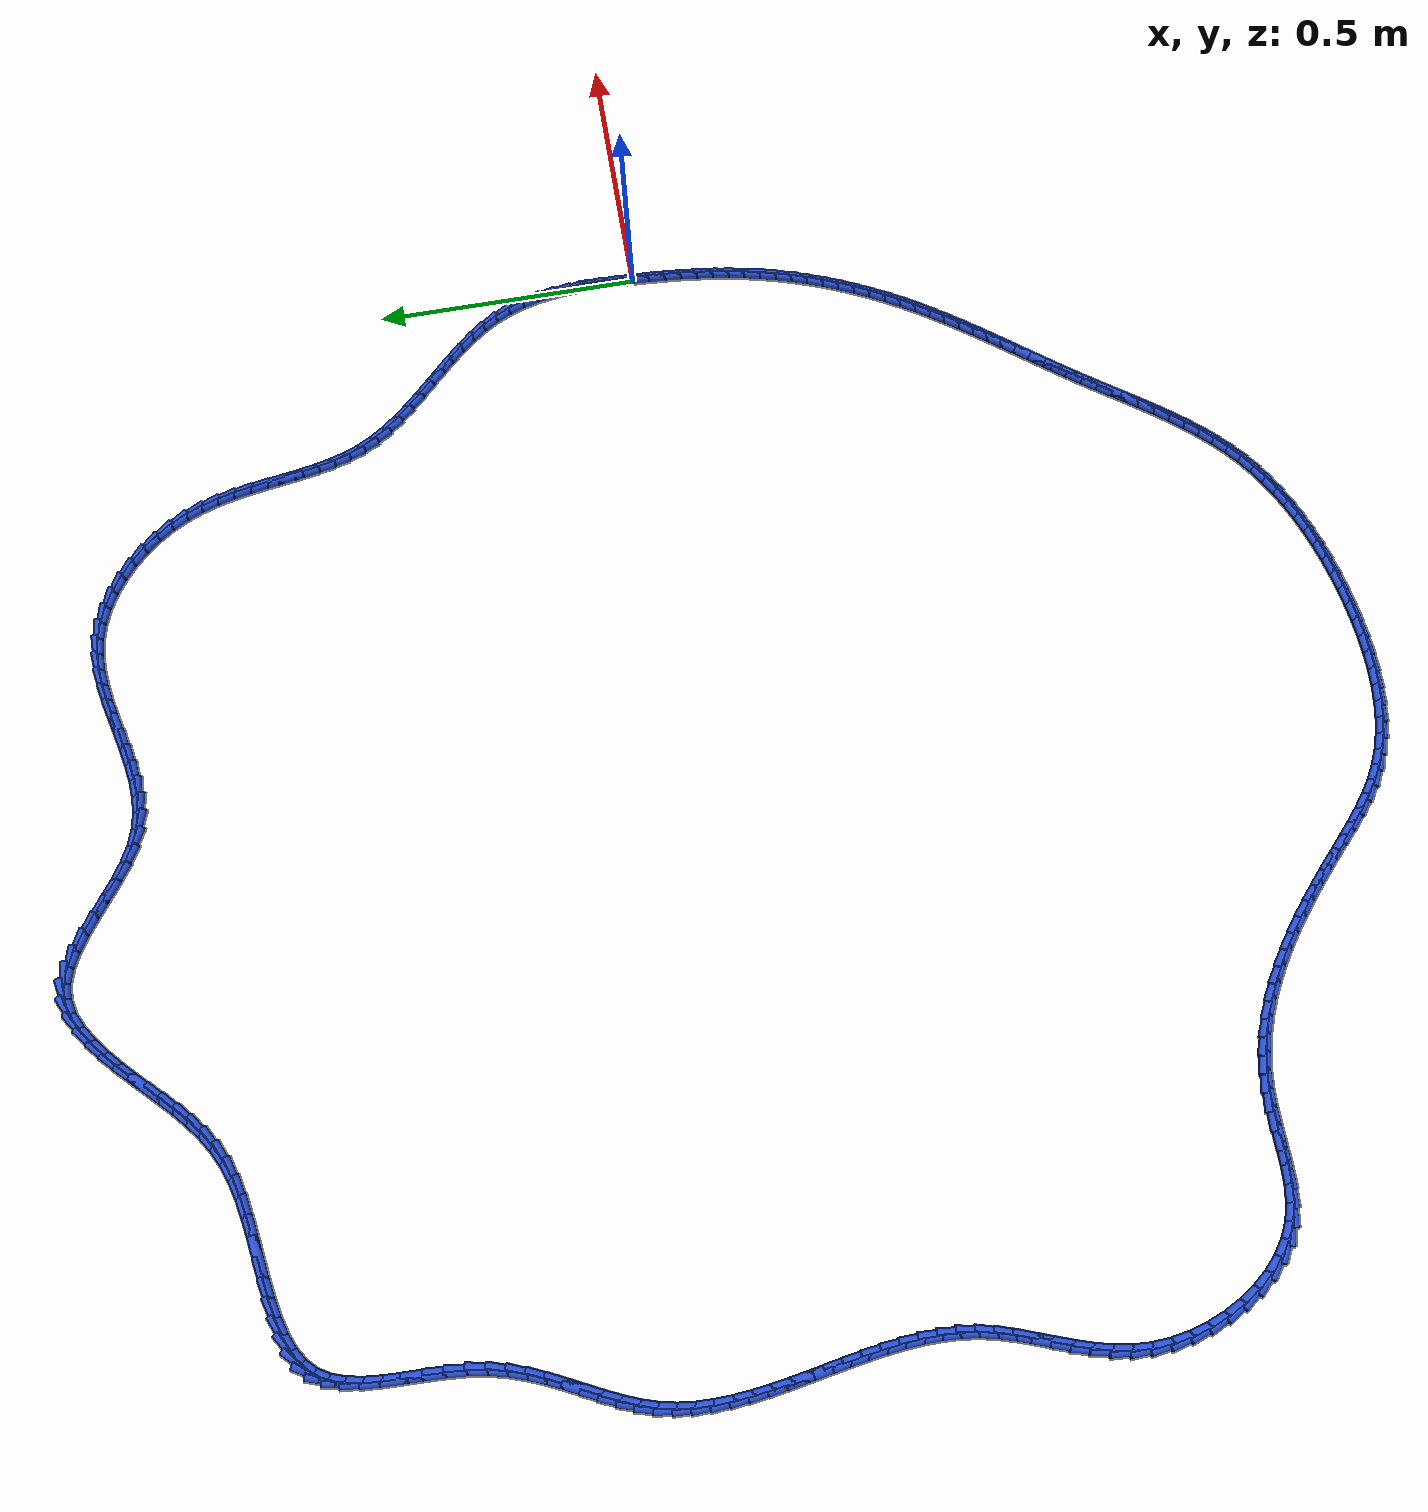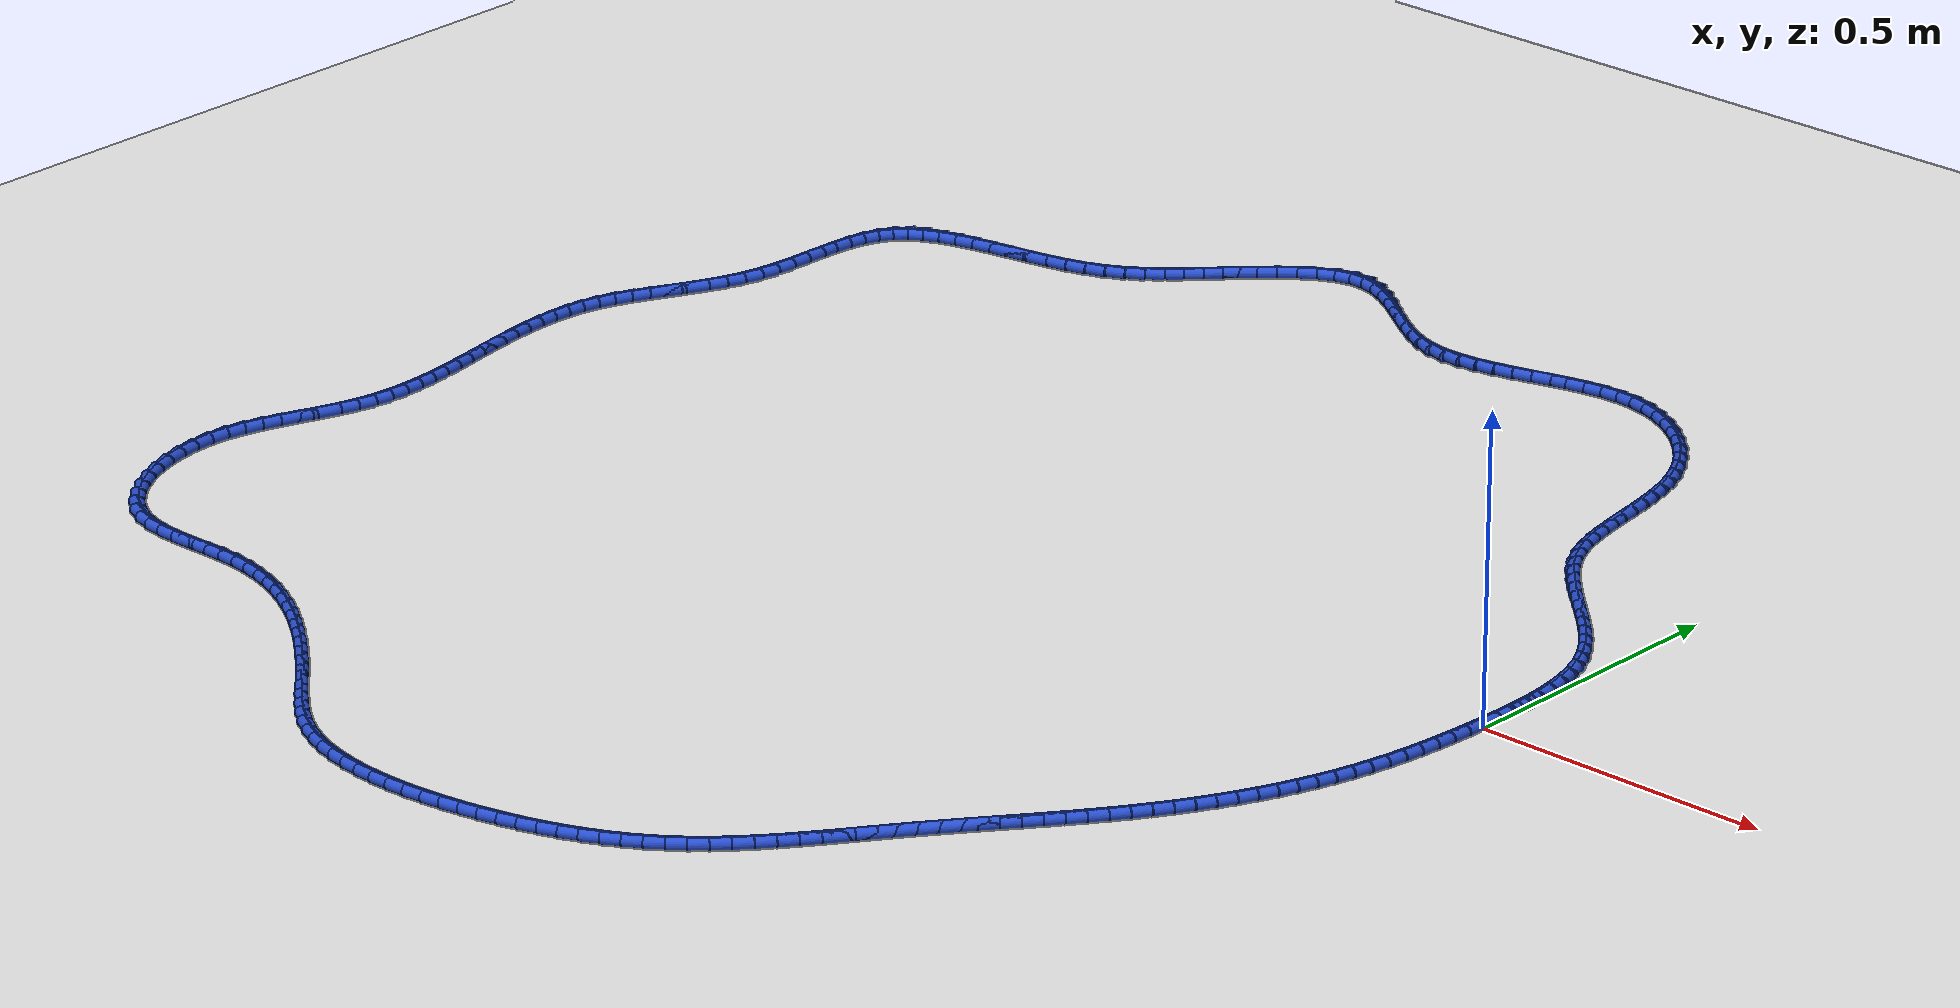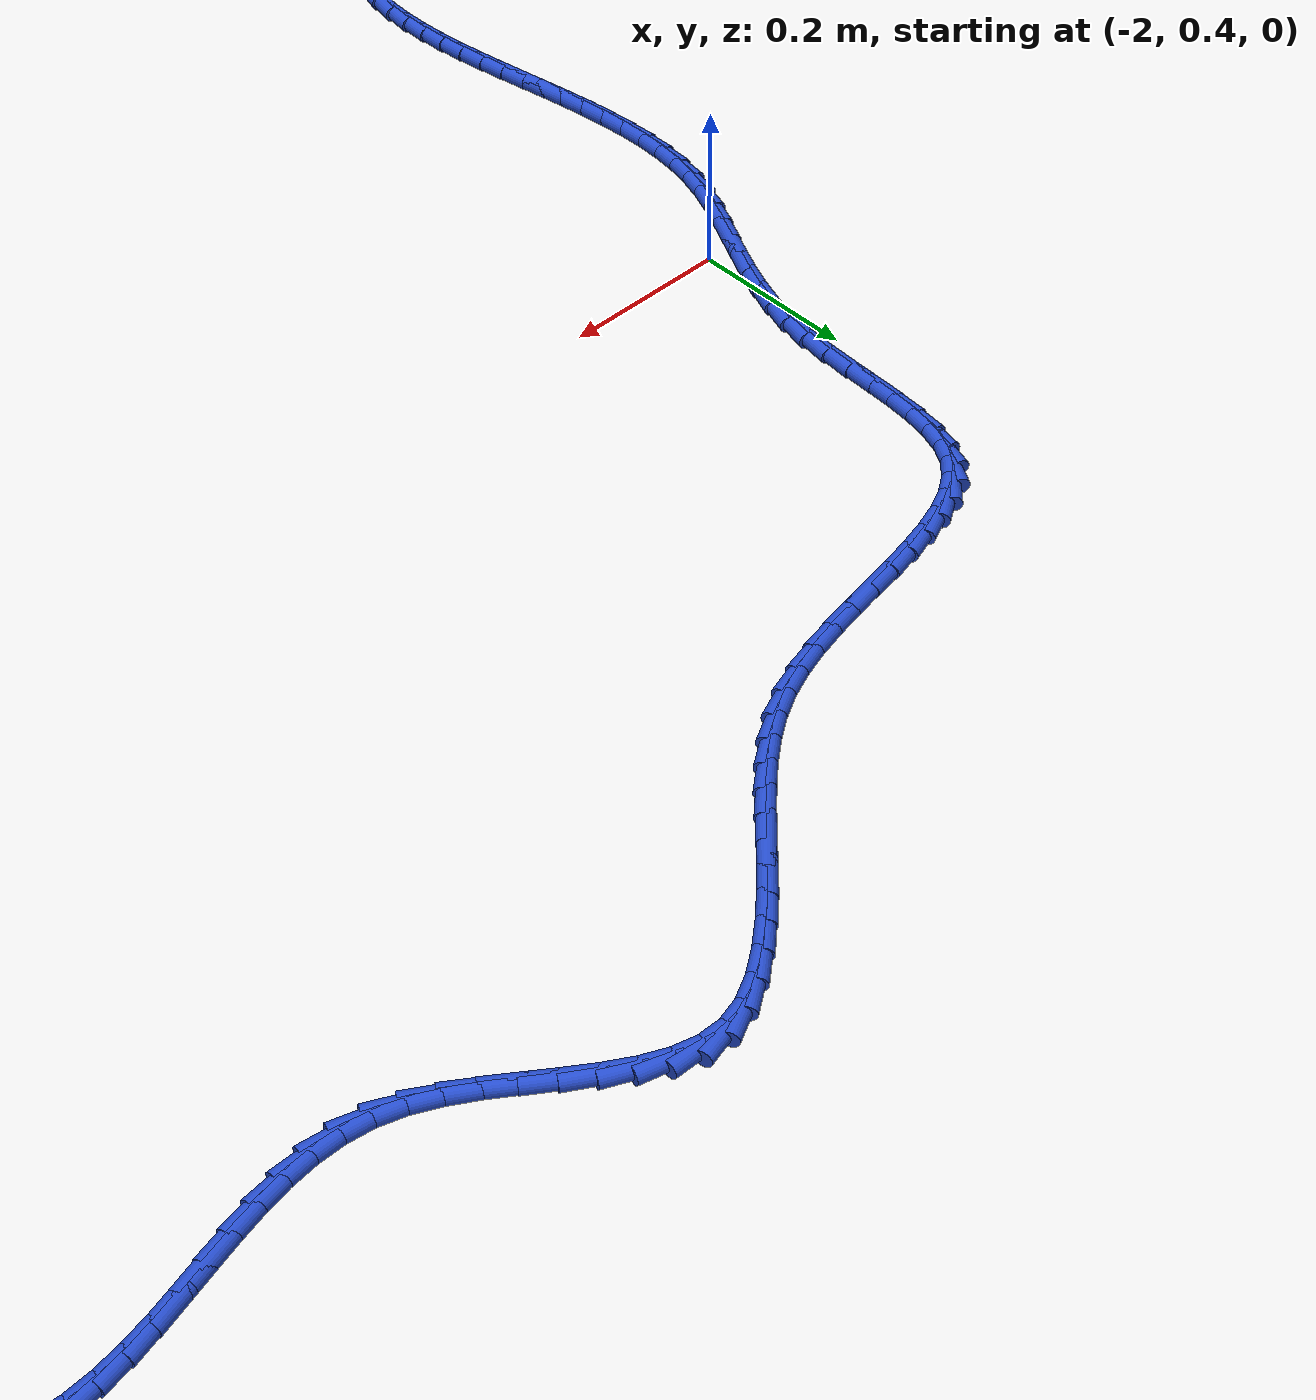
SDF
<sdf version="1.6">
 <world name="default">
  <light name="sun" type="directional">
   <pose>0 0 10 0 -0 0</pose>
   <diffuse>0.8 0.8 0.8 1</diffuse>
   <specular>0.2 0.2 0.2 1</specular>
   <attenuation>
    <range>1000</range>
    <constant>0.9</constant>
    <linear>0.01</linear>
    <quadratic>0.001</quadratic>
   </attenuation>
   <direction>-0.5 0.1 -0.9</direction>
  </light>
  <model name="ground_plane">
   <static>1</static>
   <link name="link">
    <collision name="collision">
     <geometry><plane><normal>0 0 1</normal><size>100 100</size></plane></geometry>
     <surface><friction><ode><mu>100</mu><mu2>50</mu2></ode></friction></surface>
    </collision>
    <visual name="visual">
     <cast_shadows>0</cast_shadows>
     <geometry><plane><normal>0 0 1</normal><size>100 100</size></plane></geometry>
     <material>
      <script><uri>file://media/materials/scripts/gazebo.material</uri><name>Gazebo/WhiteGlow</name></script>
     </material>
    </visual>
   </link>
  </model>
  <gravity>0 0 -9.8</gravity>
  <magnetic_field>6e-06 2.3e-05 -4.2e-05</magnetic_field>
  <atmosphere type="adiabatic"/>
  <physics name="default_physics" default="0" type="ode">
   <max_step_size>0.001</max_step_size>
   <real_time_factor>1</real_time_factor>
   <real_time_update_rate>1000</real_time_update_rate>
  </physics>
  <scene><ambient>0.4 0.4 0.4 1</ambient><background>0.7 0.7 0.7 1</background><shadows>1</shadows></scene>
  <spherical_coordinates>
   <surface_model>EARTH_WGS84</surface_model>
   <latitude_deg>0</latitude_deg>
   <longitude_deg>0</longitude_deg>
   <elevation>0</elevation>
   <heading_deg>0</heading_deg>
  </spherical_coordinates>
  <model name="line">
   <link name="link_0">
    <pose>1.202109158743303e-17 4.85722573273506e-17 0.01 0 1.57 1.536072615759685</pose>
    <collision name="collision">
     <geometry><cylinder><radius>0.01</radius><length>0.08</length></cylinder></geometry>
    </collision>
    <visual name="visual">
     <material>
      <script><name>Gazebo/Blue</name><uri>file://media/materials/scripts/gazebo.material</uri></script>
     </material>
     <geometry><cylinder><radius>0.01</radius><length>0.08</length></cylinder></geometry>
    </visual>
   </link>
   <link name="link_1">
    <pose>0.0011326819208036815 0.032606729291152346 0.01 0 1.57 1.5589145146190735</pose>
    <collision name="collision">
     <geometry><cylinder><radius>0.01</radius><length>0.08</length></cylinder></geometry>
    </collision>
    <visual name="visual">
     <material>
      <script><name>Gazebo/Blue</name><uri>file://media/materials/scripts/gazebo.material</uri></script>
     </material>
     <geometry><cylinder><radius>0.01</radius><length>0.08</length></cylinder></geometry>
    </visual>
   </link>
   <link name="link_2">
    <pose>0.0015214863202614101 0.06532784091339212 0.01 0 1.57 -1.5504343009876833</pose>
    <collision name="collision">
     <geometry><cylinder><radius>0.01</radius><length>0.08</length></cylinder></geometry>
    </collision>
    <visual name="visual">
     <material>
      <script><name>Gazebo/Blue</name><uri>file://media/materials/scripts/gazebo.material</uri></script>
     </material>
     <geometry><cylinder><radius>0.01</radius><length>0.08</length></cylinder></geometry>
    </visual>
   </link>
   <link name="link_3">
    <pose>0.000857016418377326 0.09795613012275681 0.01 0 1.57 -1.5081733999187839</pose>
    <collision name="collision">
     <geometry><cylinder><radius>0.01</radius><length>0.08</length></cylinder></geometry>
    </collision>
    <visual name="visual">
     <material>
      <script><name>Gazebo/Blue</name><uri>file://media/materials/scripts/gazebo.material</uri></script>
     </material>
     <geometry><cylinder><radius>0.01</radius><length>0.08</length></cylinder></geometry>
    </visual>
   </link>
   <link name="link_4">
    <pose>-0.0011701245648444445 0.1302843921752838 0.01 0 1.57 -1.4550653542667014</pose>
    <collision name="collision">
     <geometry><cylinder><radius>0.01</radius><length>0.08</length></cylinder></geometry>
    </collision>
    <visual name="visual">
     <material>
      <script><name>Gazebo/Blue</name><uri>file://media/materials/scripts/gazebo.material</uri></script>
     </material>
     <geometry><cylinder><radius>0.01</radius><length>0.08</length></cylinder></geometry>
    </visual>
   </link>
   <link name="link_5">
    <pose>-0.004869333409399776 0.16210542232701045 0.01 0 1.57 -1.390167169293847</pose>
    <collision name="collision">
     <geometry><cylinder><radius>0.01</radius><length>0.08</length></cylinder></geometry>
    </collision>
    <visual name="visual">
     <material>
      <script><name>Gazebo/Blue</name><uri>file://media/materials/scripts/gazebo.material</uri></script>
     </material>
     <geometry><cylinder><radius>0.01</radius><length>0.08</length></cylinder></geometry>
    </visual>
   </link>
   <link name="link_6">
    <pose>-0.010550006895284549 0.1932120158339743 0.01 0 1.57 -1.3126013579753837</pose>
    <collision name="collision">
     <geometry><cylinder><radius>0.01</radius><length>0.08</length></cylinder></geometry>
    </collision>
    <visual name="visual">
     <material>
      <script><name>Gazebo/Blue</name><uri>file://media/materials/scripts/gazebo.material</uri></script>
     </material>
     <geometry><cylinder><radius>0.01</radius><length>0.08</length></cylinder></geometry>
    </visual>
   </link>
   <link name="link_7">
    <pose>-0.01852154180249463 0.22339696795221253 0.01 0 1.57 -1.2218448880958819</pose>
    <collision name="collision">
     <geometry><cylinder><radius>0.01</radius><length>0.08</length></cylinder></geometry>
    </collision>
    <visual name="visual">
     <material>
      <script><name>Gazebo/Blue</name><uri>file://media/materials/scripts/gazebo.material</uri></script>
     </material>
     <geometry><cylinder><radius>0.01</radius><length>0.08</length></cylinder></geometry>
    </visual>
   </link>
   <link name="link_8">
    <pose>-0.02909333491102589 0.2524530739377627 0.01 0 1.57 -1.1184145608843261</pose>
    <collision name="collision">
     <geometry><cylinder><radius>0.01</radius><length>0.08</length></cylinder></geometry>
    </collision>
    <visual name="visual">
     <material>
      <script><name>Gazebo/Blue</name><uri>file://media/materials/scripts/gazebo.material</uri></script>
     </material>
     <geometry><cylinder><radius>0.01</radius><length>0.08</length></cylinder></geometry>
    </visual>
   </link>
   <link name="link_9">
    <pose>-0.04256716096853313 0.28017722478052437 0.01 0 1.57 -1.0159180892134962</pose>
    <collision name="collision">
     <geometry><cylinder><radius>0.01</radius><length>0.08</length></cylinder></geometry>
    </collision>
    <visual name="visual">
     <material>
      <script><name>Gazebo/Blue</name><uri>file://media/materials/scripts/gazebo.material</uri></script>
     </material>
     <geometry><cylinder><radius>0.01</radius><length>0.08</length></cylinder></geometry>
    </visual>
   </link>
   <link name="link_10">
    <pose>-0.05891123488468257 0.3065455513715708 0.01 0 1.57 -0.9323607290424752</pose>
    <collision name="collision">
     <geometry><cylinder><radius>0.01</radius><length>0.08</length></cylinder></geometry>
    </collision>
    <visual name="visual">
     <material>
      <script><name>Gazebo/Blue</name><uri>file://media/materials/scripts/gazebo.material</uri></script>
     </material>
     <geometry><cylinder><radius>0.01</radius><length>0.08</length></cylinder></geometry>
    </visual>
   </link>
   <link name="link_11">
    <pose>-0.07763759050579071 0.3317793155781889 0.01 0 1.57 -0.868684158812069</pose>
    <collision name="collision">
     <geometry><cylinder><radius>0.01</radius><length>0.08</length></cylinder></geometry>
    </collision>
    <visual name="visual">
     <material>
      <script><name>Gazebo/Blue</name><uri>file://media/materials/scripts/gazebo.material</uri></script>
     </material>
     <geometry><cylinder><radius>0.01</radius><length>0.08</length></cylinder></geometry>
    </visual>
   </link>
   <link name="link_12">
    <pose>-0.09822535942757539 0.3561174594421772 0.01 0 1.57 -0.8238173163707225</pose>
    <collision name="collision">
     <geometry><cylinder><radius>0.01</radius><length>0.08</length></cylinder></geometry>
    </collision>
    <visual name="visual">
     <material>
      <script><name>Gazebo/Blue</name><uri>file://media/materials/scripts/gazebo.material</uri></script>
     </material>
     <geometry><cylinder><radius>0.01</radius><length>0.08</length></cylinder></geometry>
    </visual>
   </link>
   <link name="link_13">
    <pose>-0.1201536732457546 0.3797989250053344 0.01 0 1.57 -0.7966065555392438</pose>
    <collision name="collision">
     <geometry><cylinder><radius>0.01</radius><length>0.08</length></cylinder></geometry>
    </collision>
    <visual name="visual">
     <material>
      <script><name>Gazebo/Blue</name><uri>file://media/materials/scripts/gazebo.material</uri></script>
     </material>
     <geometry><cylinder><radius>0.01</radius><length>0.08</length></cylinder></geometry>
    </visual>
   </link>
   <link name="link_14">
    <pose>-0.14290166355604628 0.40306265430945915 0.01 0 1.57 -0.7862248542065737</pose>
    <collision name="collision">
     <geometry><cylinder><radius>0.01</radius><length>0.08</length></cylinder></geometry>
    </collision>
    <visual name="visual">
     <material>
      <script><name>Gazebo/Blue</name><uri>file://media/materials/scripts/gazebo.material</uri></script>
     </material>
     <geometry><cylinder><radius>0.01</radius><length>0.08</length></cylinder></geometry>
    </visual>
   </link>
   <link name="link_15">
    <pose>-0.16594846195416818 0.4261475893963499 0.01 0 1.57 -0.7923666404888908</pose>
    <collision name="collision">
     <geometry><cylinder><radius>0.01</radius><length>0.08</length></cylinder></geometry>
    </collision>
    <visual name="visual">
     <material>
      <script><name>Gazebo/Blue</name><uri>file://media/materials/scripts/gazebo.material</uri></script>
     </material>
     <geometry><cylinder><radius>0.01</radius><length>0.08</length></cylinder></geometry>
    </visual>
   </link>
   <link name="link_16">
    <pose>-0.18877320003583842 0.4492926723078053 0.01 0 1.57 -0.8153142004422874</pose>
    <collision name="collision">
     <geometry><cylinder><radius>0.01</radius><length>0.08</length></cylinder></geometry>
    </collision>
    <visual name="visual">
     <material>
      <script><name>Gazebo/Blue</name><uri>file://media/materials/scripts/gazebo.material</uri></script>
     </material>
     <geometry><cylinder><radius>0.01</radius><length>0.08</length></cylinder></geometry>
    </visual>
   </link>
   <link name="link_17">
    <pose>-0.2108550093967748 0.4727368450856239 0.01 0 1.57 -0.8559100244586151</pose>
    <collision name="collision">
     <geometry><cylinder><radius>0.01</radius><length>0.08</length></cylinder></geometry>
    </collision>
    <visual name="visual">
     <material>
      <script><name>Gazebo/Blue</name><uri>file://media/materials/scripts/gazebo.material</uri></script>
     </material>
     <geometry><cylinder><radius>0.01</radius><length>0.08</length></cylinder></geometry>
    </visual>
   </link>
   <link name="link_18">
    <pose>-0.23167302163269515 0.4967190497716043 0.01 0 1.57 -0.9154097171607953</pose>
    <collision name="collision">
     <geometry><cylinder><radius>0.01</radius><length>0.08</length></cylinder></geometry>
    </collision>
    <visual name="visual">
     <material>
      <script><name>Gazebo/Blue</name><uri>file://media/materials/scripts/gazebo.material</uri></script>
     </material>
     <geometry><cylinder><radius>0.01</radius><length>0.08</length></cylinder></geometry>
    </visual>
   </link>
   <link name="link_19">
    <pose>-0.2507063683393175 0.521478228407545 0.01 0 1.57 -0.9951305203033091</pose>
    <collision name="collision">
     <geometry><cylinder><radius>0.01</radius><length>0.08</length></cylinder></geometry>
    </collision>
    <visual name="visual">
     <material>
      <script><name>Gazebo/Blue</name><uri>file://media/materials/scripts/gazebo.material</uri></script>
     </material>
     <geometry><cylinder><radius>0.01</radius><length>0.08</length></cylinder></geometry>
    </visual>
   </link>
   <link name="link_20">
    <pose>-0.2674341811123598 0.5472533230352448 0.01 0 1.57 -1.0954069438895215</pose>
    <collision name="collision">
     <geometry><cylinder><radius>0.01</radius><length>0.08</length></cylinder></geometry>
    </collision>
    <visual name="visual">
     <material>
      <script><name>Gazebo/Blue</name><uri>file://media/materials/scripts/gazebo.material</uri></script>
     </material>
     <geometry><cylinder><radius>0.01</radius><length>0.08</length></cylinder></geometry>
    </visual>
   </link>
   <link name="link_21">
    <pose>-0.28134601725721703 0.5742789513794768 0.01 0 1.57 -1.1996570364553794</pose>
    <collision name="collision">
     <geometry><cylinder><radius>0.01</radius><length>0.08</length></cylinder></geometry>
    </collision>
    <visual name="visual">
     <material>
      <script><name>Gazebo/Blue</name><uri>file://media/materials/scripts/gazebo.material</uri></script>
     </material>
     <geometry><cylinder><radius>0.01</radius><length>0.08</length></cylinder></geometry>
    </visual>
   </link>
   <link name="link_22">
    <pose>-0.29237076668710016 0.6026075072651954 0.01 0 1.57 -1.284765469541798</pose>
    <collision name="collision">
     <geometry><cylinder><radius>0.01</radius><length>0.08</length></cylinder></geometry>
    </collision>
    <visual name="visual">
     <material>
      <script><name>Gazebo/Blue</name><uri>file://media/materials/scripts/gazebo.material</uri></script>
     </material>
     <geometry><cylinder><radius>0.01</radius><length>0.08</length></cylinder></geometry>
    </visual>
   </link>
   <link name="link_23">
    <pose>-0.30102853639954247 0.6320461628314878 0.01 0 1.57 -1.348655534851808</pose>
    <collision name="collision">
     <geometry><cylinder><radius>0.01</radius><length>0.08</length></cylinder></geometry>
    </collision>
    <visual name="visual">
     <material>
      <script><name>Gazebo/Blue</name><uri>file://media/materials/scripts/gazebo.material</uri></script>
     </material>
     <geometry><cylinder><radius>0.01</radius><length>0.08</length></cylinder></geometry>
    </visual>
   </link>
   <link name="link_24">
    <pose>-0.30788107803195985 0.6623848170887213 0.01 0 1.57 -1.3919565973893917</pose>
    <collision name="collision">
     <geometry><cylinder><radius>0.01</radius><length>0.08</length></cylinder></geometry>
    </collision>
    <visual name="visual">
     <material>
      <script><name>Gazebo/Blue</name><uri>file://media/materials/scripts/gazebo.material</uri></script>
     </material>
     <geometry><cylinder><radius>0.01</radius><length>0.08</length></cylinder></geometry>
    </visual>
   </link>
   <link name="link_25">
    <pose>-0.3134901432217676 0.6934133690472625 0.01 0 1.57 -1.4156706774662529</pose>
    <collision name="collision">
     <geometry><cylinder><radius>0.01</radius><length>0.08</length></cylinder></geometry>
    </collision>
    <visual name="visual">
     <material>
      <script><name>Gazebo/Blue</name><uri>file://media/materials/scripts/gazebo.material</uri></script>
     </material>
     <geometry><cylinder><radius>0.01</radius><length>0.08</length></cylinder></geometry>
    </visual>
   </link>
   <link name="link_26">
    <pose>-0.3184174836063813 0.7249217177174787 0.01 0 1.57 -1.4206552530040042</pose>
    <collision name="collision">
     <geometry><cylinder><radius>0.01</radius><length>0.08</length></cylinder></geometry>
    </collision>
    <visual name="visual">
     <material>
      <script><name>Gazebo/Blue</name><uri>file://media/materials/scripts/gazebo.material</uri></script>
     </material>
     <geometry><cylinder><radius>0.01</radius><length>0.08</length></cylinder></geometry>
    </visual>
   </link>
   <link name="link_27">
    <pose>-0.3232248508232165 0.7566997621097367 0.01 0 1.57 -1.4073939985921065</pose>
    <collision name="collision">
     <geometry><cylinder><radius>0.01</radius><length>0.08</length></cylinder></geometry>
    </collision>
    <visual name="visual">
     <material>
      <script><name>Gazebo/Blue</name><uri>file://media/materials/scripts/gazebo.material</uri></script>
     </material>
     <geometry><cylinder><radius>0.01</radius><length>0.08</length></cylinder></geometry>
    </visual>
   </link>
   <link name="link_28">
    <pose>-0.32847399650968884 0.7885374012344033 0.01 0 1.57 -1.3759738268489967</pose>
    <collision name="collision">
     <geometry><cylinder><radius>0.01</radius><length>0.08</length></cylinder></geometry>
    </collision>
    <visual name="visual">
     <material>
      <script><name>Gazebo/Blue</name><uri>file://media/materials/scripts/gazebo.material</uri></script>
     </material>
     <geometry><cylinder><radius>0.01</radius><length>0.08</length></cylinder></geometry>
    </visual>
   </link>
   <link name="link_29">
    <pose>-0.33472667230321385 0.8202245341018459 0.01 0 1.57 -1.326228524526145</pose>
    <collision name="collision">
     <geometry><cylinder><radius>0.01</radius><length>0.08</length></cylinder></geometry>
    </collision>
    <visual name="visual">
     <material>
      <script><name>Gazebo/Blue</name><uri>file://media/materials/scripts/gazebo.material</uri></script>
     </material>
     <geometry><cylinder><radius>0.01</radius><length>0.08</length></cylinder></geometry>
    </visual>
   </link>
   <link name="link_30">
    <pose>-0.3425446298412069 0.8515510597224313 0.01 0 1.57 -1.2580546531642047</pose>
    <collision name="collision">
     <geometry><cylinder><radius>0.01</radius><length>0.08</length></cylinder></geometry>
    </collision>
    <visual name="visual">
     <material>
      <script><name>Gazebo/Blue</name><uri>file://media/materials/scripts/gazebo.material</uri></script>
     </material>
     <geometry><cylinder><radius>0.01</radius><length>0.08</length></cylinder></geometry>
    </visual>
   </link>
   <link name="link_31">
    <pose>-0.3524896207610839 0.8823068771065266 0.01 0 1.57 -1.1719134885823648</pose>
    <collision name="collision">
     <geometry><cylinder><radius>0.01</radius><length>0.08</length></cylinder></geometry>
    </collision>
    <visual name="visual">
     <material>
      <script><name>Gazebo/Blue</name><uri>file://media/materials/scripts/gazebo.material</uri></script>
     </material>
     <geometry><cylinder><radius>0.01</radius><length>0.08</length></cylinder></geometry>
    </visual>
   </link>
   <link name="link_32">
    <pose>-0.36512339670026017 0.9122818852644988 0.01 0 1.57 -1.0725928964099547</pose>
    <collision name="collision">
     <geometry><cylinder><radius>0.01</radius><length>0.08</length></cylinder></geometry>
    </collision>
    <visual name="visual">
     <material>
      <script><name>Gazebo/Blue</name><uri>file://media/materials/scripts/gazebo.material</uri></script>
     </material>
     <geometry><cylinder><radius>0.01</radius><length>0.08</length></cylinder></geometry>
    </visual>
   </link>
   <link name="link_33">
    <pose>-0.3808754534632304 0.9412393610753276 0.01 0 1.57 -0.9746524733674867</pose>
    <collision name="collision">
     <geometry><cylinder><radius>0.01</radius><length>0.08</length></cylinder></geometry>
    </collision>
    <visual name="visual">
     <material>
      <script><name>Gazebo/Blue</name><uri>file://media/materials/scripts/gazebo.material</uri></script>
     </material>
     <geometry><cylinder><radius>0.01</radius><length>0.08</length></cylinder></geometry>
    </visual>
   </link>
   <link name="link_34">
    <pose>-0.3995921944709324 0.9688252091879533 0.01 0 1.57 -0.879632615308312</pose>
    <collision name="collision">
     <geometry><cylinder><radius>0.01</radius><length>0.08</length></cylinder></geometry>
    </collision>
    <visual name="visual">
     <material>
      <script><name>Gazebo/Blue</name><uri>file://media/materials/scripts/gazebo.material</uri></script>
     </material>
     <geometry><cylinder><radius>0.01</radius><length>0.08</length></cylinder></geometry>
    </visual>
   </link>
   <link name="link_35">
    <pose>-0.420959379234172 0.9946529978077153 0.01 0 1.57 -0.7849742737387273</pose>
    <collision name="collision">
     <geometry><cylinder><radius>0.01</radius><length>0.08</length></cylinder></geometry>
    </collision>
    <visual name="visual">
     <material>
      <script><name>Gazebo/Blue</name><uri>file://media/materials/scripts/gazebo.material</uri></script>
     </material>
     <geometry><cylinder><radius>0.01</radius><length>0.08</length></cylinder></geometry>
    </visual>
   </link>
   <link name="link_36">
    <pose>-0.4446627622897317 1.0183362941387188 0.01 0 1.57 -0.6881549010183486</pose>
    <collision name="collision">
     <geometry><cylinder><radius>0.01</radius><length>0.08</length></cylinder></geometry>
    </collision>
    <visual name="visual">
     <material>
      <script><name>Gazebo/Blue</name><uri>file://media/materials/scripts/gazebo.material</uri></script>
     </material>
     <geometry><cylinder><radius>0.01</radius><length>0.08</length></cylinder></geometry>
    </visual>
   </link>
   <link name="link_37">
    <pose>-0.47038809817439386 1.0394886653850695 0.01 0 1.57 -0.5866466428776934</pose>
    <collision name="collision">
     <geometry><cylinder><radius>0.01</radius><length>0.08</length></cylinder></geometry>
    </collision>
    <visual name="visual">
     <material>
      <script><name>Gazebo/Blue</name><uri>file://media/materials/scripts/gazebo.material</uri></script>
     </material>
     <geometry><cylinder><radius>0.01</radius><length>0.08</length></cylinder></geometry>
    </visual>
   </link>
   <link name="link_38">
    <pose>-0.4978211414249404 1.0577236787508715 0.01 0 1.57 -0.47791888875416527</pose>
    <collision name="collision">
     <geometry><cylinder><radius>0.01</radius><length>0.08</length></cylinder></geometry>
    </collision>
    <visual name="visual">
     <material>
      <script><name>Gazebo/Blue</name><uri>file://media/materials/scripts/gazebo.material</uri></script>
     </material>
     <geometry><cylinder><radius>0.01</radius><length>0.08</length></cylinder></geometry>
    </visual>
   </link>
   <link name="link_39">
    <pose>-0.5266476465781543 1.0726549014402307 0.01 0 1.57 -0.3595430257160499</pose>
    <collision name="collision">
     <geometry><cylinder><radius>0.01</radius><length>0.08</length></cylinder></geometry>
    </collision>
    <visual name="visual">
     <material>
      <script><name>Gazebo/Blue</name><uri>file://media/materials/scripts/gazebo.material</uri></script>
     </material>
     <geometry><cylinder><radius>0.01</radius><length>0.08</length></cylinder></geometry>
    </visual>
   </link>
   <link name="link_40">
    <pose>-0.5565533681708177 1.083895900657252 0.01 0 1.57 -0.2294745875804386</pose>
    <collision name="collision">
     <geometry><cylinder><radius>0.01</radius><length>0.08</length></cylinder></geometry>
    </collision>
    <visual name="visual">
     <material>
      <script><name>Gazebo/Blue</name><uri>file://media/materials/scripts/gazebo.material</uri></script>
     </material>
     <geometry><cylinder><radius>0.01</radius><length>0.08</length></cylinder></geometry>
    </visual>
   </link>
   <link name="link_41">
    <pose>-0.587224060739713 1.0910602436060408 0.01 0 1.57 -0.08997493502434484</pose>
    <collision name="collision">
     <geometry><cylinder><radius>0.01</radius><length>0.08</length></cylinder></geometry>
    </collision>
    <visual name="visual">
     <material>
      <script><name>Gazebo/Blue</name><uri>file://media/materials/scripts/gazebo.material</uri></script>
     </material>
     <geometry><cylinder><radius>0.01</radius><length>0.08</length></cylinder></geometry>
    </visual>
   </link>
   <link name="link_42">
    <pose>-0.6183667220842624 1.0938698884483016 0.01 0 1.57 0.03368978004114141</pose>
    <collision name="collision">
     <geometry><cylinder><radius>0.01</radius><length>0.08</length></cylinder></geometry>
    </collision>
    <visual name="visual">
     <material>
      <script><name>Gazebo/Blue</name><uri>file://media/materials/scripts/gazebo.material</uri></script>
     </material>
     <geometry><cylinder><radius>0.01</radius><length>0.08</length></cylinder></geometry>
    </visual>
   </link>
   <link name="link_43">
    <pose>-0.6498377788011244 1.092809234158156 0.01 0 1.57 0.12914417288525487</pose>
    <collision name="collision">
     <geometry><cylinder><radius>0.01</radius><length>0.08</length></cylinder></geometry>
    </collision>
    <visual name="visual">
     <material>
      <script><name>Gazebo/Blue</name><uri>file://media/materials/scripts/gazebo.material</uri></script>
     </material>
     <geometry><cylinder><radius>0.01</radius><length>0.08</length></cylinder></geometry>
    </visual>
   </link>
   <link name="link_44">
    <pose>-0.6815577795448817 1.0886898540887027 0.01 0 1.57 0.19701346721089535</pose>
    <collision name="collision">
     <geometry><cylinder><radius>0.01</radius><length>0.08</length></cylinder></geometry>
    </collision>
    <visual name="visual">
     <material>
      <script><name>Gazebo/Blue</name><uri>file://media/materials/scripts/gazebo.material</uri></script>
     </material>
     <geometry><cylinder><radius>0.01</radius><length>0.08</length></cylinder></geometry>
    </visual>
   </link>
   <link name="link_45">
    <pose>-0.7134475190999371 1.082324577438122 0.01 0 1.57 0.23918075960787294</pose>
    <collision name="collision">
     <geometry><cylinder><radius>0.01</radius><length>0.08</length></cylinder></geometry>
    </collision>
    <visual name="visual">
     <material>
      <script><name>Gazebo/Blue</name><uri>file://media/materials/scripts/gazebo.material</uri></script>
     </material>
     <geometry><cylinder><radius>0.01</radius><length>0.08</length></cylinder></geometry>
    </visual>
   </link>
   <link name="link_46">
    <pose>-0.7454277922506934 1.0745262334045957 0.01 0 1.57 0.25731610571881175</pose>
    <collision name="collision">
     <geometry><cylinder><radius>0.01</radius><length>0.08</length></cylinder></geometry>
    </collision>
    <visual name="visual">
     <material>
      <script><name>Gazebo/Blue</name><uri>file://media/materials/scripts/gazebo.material</uri></script>
     </material>
     <geometry><cylinder><radius>0.01</radius><length>0.08</length></cylinder></geometry>
    </visual>
   </link>
   <link name="link_47">
    <pose>-0.777419393781553 1.0661076511863037 0.01 0 1.57 0.2521903811376211</pose>
    <collision name="collision">
     <geometry><cylinder><radius>0.01</radius><length>0.08</length></cylinder></geometry>
    </collision>
    <visual name="visual">
     <material>
      <script><name>Gazebo/Blue</name><uri>file://media/materials/scripts/gazebo.material</uri></script>
     </material>
     <geometry><cylinder><radius>0.01</radius><length>0.08</length></cylinder></geometry>
    </visual>
   </link>
   <link name="link_48">
    <pose>-0.8093431184769193 1.057881659981427 0.01 0 1.57 0.22343490931786864</pose>
    <collision name="collision">
     <geometry><cylinder><radius>0.01</radius><length>0.08</length></cylinder></geometry>
    </collision>
    <visual name="visual">
     <material>
      <script><name>Gazebo/Blue</name><uri>file://media/materials/scripts/gazebo.material</uri></script>
     </material>
     <geometry><cylinder><radius>0.01</radius><length>0.08</length></cylinder></geometry>
    </visual>
   </link>
   <link name="link_49">
    <pose>-0.8411197611211949 1.050661088988147 0.01 0 1.57 0.16958395582606758</pose>
    <collision name="collision">
     <geometry><cylinder><radius>0.01</radius><length>0.08</length></cylinder></geometry>
    </collision>
    <visual name="visual">
     <material>
      <script><name>Gazebo/Blue</name><uri>file://media/materials/scripts/gazebo.material</uri></script>
     </material>
     <geometry><cylinder><radius>0.01</radius><length>0.08</length></cylinder></geometry>
    </visual>
   </link>
   <link name="link_50">
    <pose>-0.8726701164987825 1.0452587674046439 0.01 0 1.57 0.08846287012202927</pose>
    <collision name="collision">
     <geometry><cylinder><radius>0.01</radius><length>0.08</length></cylinder></geometry>
    </collision>
    <visual name="visual">
     <material>
      <script><name>Gazebo/Blue</name><uri>file://media/materials/scripts/gazebo.material</uri></script>
     </material>
     <geometry><cylinder><radius>0.01</radius><length>0.08</length></cylinder></geometry>
    </visual>
   </link>
   <link name="link_51">
    <pose>-0.9039149793940853 1.0424875244290988 0.01 0 1.57 -0.021793737170809055</pose>
    <collision name="collision">
     <geometry><cylinder><radius>0.01</radius><length>0.08</length></cylinder></geometry>
    </collision>
    <visual name="visual">
     <material>
      <script><name>Gazebo/Blue</name><uri>file://media/materials/scripts/gazebo.material</uri></script>
     </material>
     <geometry><cylinder><radius>0.01</radius><length>0.08</length></cylinder></geometry>
    </visual>
   </link>
   <link name="link_52">
    <pose>-0.9347751445915056 1.0431601892596924 0.01 0 1.57 -0.16077165922590647</pose>
    <collision name="collision">
     <geometry><cylinder><radius>0.01</radius><length>0.08</length></cylinder></geometry>
    </collision>
    <visual name="visual">
     <material>
      <script><name>Gazebo/Blue</name><uri>file://media/materials/scripts/gazebo.material</uri></script>
     </material>
     <geometry><cylinder><radius>0.01</radius><length>0.08</length></cylinder></geometry>
    </visual>
   </link>
   <link name="link_53">
    <pose>-0.9651714068754462 1.0480895910946055 0.01 0 1.57 -0.3220942035098514</pose>
    <collision name="collision">
     <geometry><cylinder><radius>0.01</radius><length>0.08</length></cylinder></geometry>
    </collision>
    <visual name="visual">
     <material>
      <script><name>Gazebo/Blue</name><uri>file://media/materials/scripts/gazebo.material</uri></script>
     </material>
     <geometry><cylinder><radius>0.01</radius><length>0.08</length></cylinder></geometry>
    </visual>
   </link>
   <link name="link_54">
    <pose>-0.9950271691410228 1.0580529130520584 0.01 0 1.57 -0.46623125615261896</pose>
    <collision name="collision">
     <geometry><cylinder><radius>0.01</radius><length>0.08</length></cylinder></geometry>
    </collision>
    <visual name="visual">
     <material>
      <script><name>Gazebo/Blue</name><uri>file://media/materials/scripts/gazebo.material</uri></script>
     </material>
     <geometry><cylinder><radius>0.01</radius><length>0.08</length></cylinder></geometry>
    </visual>
   </link>
   <link name="link_55">
    <pose>-1.0243406751589712 1.0728044584223764 0.01 0 1.57 -0.5613428617239103</pose>
    <collision name="collision">
     <geometry><cylinder><radius>0.01</radius><length>0.08</length></cylinder></geometry>
    </collision>
    <visual name="visual">
     <material>
      <script><name>Gazebo/Blue</name><uri>file://media/materials/scripts/gazebo.material</uri></script>
     </material>
     <geometry><cylinder><radius>0.01</radius><length>0.08</length></cylinder></geometry>
    </visual>
   </link>
   <link name="link_56">
    <pose>-1.0531943299261233 1.0909482657542016 0.01 0 1.57 -0.6140735378528087</pose>
    <collision name="collision">
     <geometry><cylinder><radius>0.01</radius><length>0.08</length></cylinder></geometry>
    </collision>
    <visual name="visual">
     <material>
      <script><name>Gazebo/Blue</name><uri>file://media/materials/scripts/gazebo.material</uri></script>
     </material>
     <geometry><cylinder><radius>0.01</radius><length>0.08</length></cylinder></geometry>
    </visual>
   </link>
   <link name="link_57">
    <pose>-1.0816750186736275 1.1110271404629344 0.01 0 1.57 -0.6299917456313363</pose>
    <collision name="collision">
     <geometry><cylinder><radius>0.01</radius><length>0.08</length></cylinder></geometry>
    </collision>
    <visual name="visual">
     <material>
      <script><name>Gazebo/Blue</name><uri>file://media/materials/scripts/gazebo.material</uri></script>
     </material>
     <geometry><cylinder><radius>0.01</radius><length>0.08</length></cylinder></geometry>
    </visual>
   </link>
   <link name="link_58">
    <pose>-1.1098696266326336 1.1315838879639775 0.01 0 1.57 -0.6102616202183898</pose>
    <collision name="collision">
     <geometry><cylinder><radius>0.01</radius><length>0.08</length></cylinder></geometry>
    </collision>
    <visual name="visual">
     <material>
      <script><name>Gazebo/Blue</name><uri>file://media/materials/scripts/gazebo.material</uri></script>
     </material>
     <geometry><cylinder><radius>0.01</radius><length>0.08</length></cylinder></geometry>
    </visual>
   </link>
   <link name="link_59">
    <pose>-1.1378650390342928 1.1511613136727337 0.01 0 1.57 -0.5511886259884812</pose>
    <collision name="collision">
     <geometry><cylinder><radius>0.01</radius><length>0.08</length></cylinder></geometry>
    </collision>
    <visual name="visual">
     <material>
      <script><name>Gazebo/Blue</name><uri>file://media/materials/scripts/gazebo.material</uri></script>
     </material>
     <geometry><cylinder><radius>0.01</radius><length>0.08</length></cylinder></geometry>
    </visual>
   </link>
   <link name="link_60">
    <pose>-1.165748141109753 1.168302223004603 0.01 0 1.57 -0.443881770155141</pose>
    <collision name="collision">
     <geometry><cylinder><radius>0.01</radius><length>0.08</length></cylinder></geometry>
    </collision>
    <visual name="visual">
     <material>
      <script><name>Gazebo/Blue</name><uri>file://media/materials/scripts/gazebo.material</uri></script>
     </material>
     <geometry><cylinder><radius>0.01</radius><length>0.08</length></cylinder></geometry>
    </visual>
   </link>
   <link name="link_61">
    <pose>-1.193605818090165 1.1815494213749886 0.01 0 1.57 -0.27562848375242255</pose>
    <collision name="collision">
     <geometry><cylinder><radius>0.01</radius><length>0.08</length></cylinder></geometry>
    </collision>
    <visual name="visual">
     <material>
      <script><name>Gazebo/Blue</name><uri>file://media/materials/scripts/gazebo.material</uri></script>
     </material>
     <geometry><cylinder><radius>0.01</radius><length>0.08</length></cylinder></geometry>
    </visual>
   </link>
   <link name="link_62">
    <pose>-1.2215249552066774 1.1894457141992918 0.01 0 1.57 -0.038751175619395624</pose>
    <collision name="collision">
     <geometry><cylinder><radius>0.01</radius><length>0.08</length></cylinder></geometry>
    </collision>
    <visual name="visual">
     <material>
      <script><name>Gazebo/Blue</name><uri>file://media/materials/scripts/gazebo.material</uri></script>
     </material>
     <geometry><cylinder><radius>0.01</radius><length>0.08</length></cylinder></geometry>
    </visual>
   </link>
   <link name="link_63">
    <pose>-1.249592437690441 1.1905339068929148 0.01 0 1.57 0.2420069220241617</pose>
    <collision name="collision">
     <geometry><cylinder><radius>0.01</radius><length>0.08</length></cylinder></geometry>
    </collision>
    <visual name="visual">
     <material>
      <script><name>Gazebo/Blue</name><uri>file://media/materials/scripts/gazebo.material</uri></script>
     </material>
     <geometry><cylinder><radius>0.01</radius><length>0.08</length></cylinder></geometry>
    </visual>
   </link>
   <link name="link_64">
    <pose>-1.277856012216005 1.1835571888001408 0.01 0 1.57 0.4649869453436106</pose>
    <collision name="collision">
     <geometry><cylinder><radius>0.01</radius><length>0.08</length></cylinder></geometry>
    </collision>
    <visual name="visual">
     <material>
      <script><name>Gazebo/Blue</name><uri>file://media/materials/scripts/gazebo.material</uri></script>
     </material>
     <geometry><cylinder><radius>0.01</radius><length>0.08</length></cylinder></geometry>
    </visual>
   </link>
   <link name="link_65">
    <pose>-1.305931009957357 1.169472656073266 0.01 0 1.57 0.6056995610645312</pose>
    <collision name="collision">
     <geometry><cylinder><radius>0.01</radius><length>0.08</length></cylinder></geometry>
    </collision>
    <visual name="visual">
     <material>
      <script><name>Gazebo/Blue</name><uri>file://media/materials/scripts/gazebo.material</uri></script>
     </material>
     <geometry><cylinder><radius>0.01</radius><length>0.08</length></cylinder></geometry>
    </visual>
   </link>
   <link name="link_66">
    <pose>-1.3331641405651742 1.1506127094465664 0.01 0 1.57 0.6914183590811336</pose>
    <collision name="collision">
     <geometry><cylinder><radius>0.01</radius><length>0.08</length></cylinder></geometry>
    </collision>
    <visual name="visual">
     <material>
      <script><name>Gazebo/Blue</name><uri>file://media/materials/scripts/gazebo.material</uri></script>
     </material>
     <geometry><cylinder><radius>0.01</radius><length>0.08</length></cylinder></geometry>
    </visual>
   </link>
   <link name="link_67">
    <pose>-1.3589184625712203 1.1292952540077432 0.01 0 1.57 0.7466228994218603</pose>
    <collision name="collision">
     <geometry><cylinder><radius>0.01</radius><length>0.08</length></cylinder></geometry>
    </collision>
    <visual name="visual">
     <material>
      <script><name>Gazebo/Blue</name><uri>file://media/materials/scripts/gazebo.material</uri></script>
     </material>
     <geometry><cylinder><radius>0.01</radius><length>0.08</length></cylinder></geometry>
    </visual>
   </link>
   <link name="link_68">
    <pose>-1.3830774864186108 1.106940710463152 0.01 0 1.57 0.7837222870269861</pose>
    <collision name="collision">
     <geometry><cylinder><radius>0.01</radius><length>0.08</length></cylinder></geometry>
    </collision>
    <visual name="visual">
     <material>
      <script><name>Gazebo/Blue</name><uri>file://media/materials/scripts/gazebo.material</uri></script>
     </material>
     <geometry><cylinder><radius>0.01</radius><length>0.08</length></cylinder></geometry>
    </visual>
   </link>
   <link name="link_69">
    <pose>-1.4060755950025408 1.0840195569575513 0.01 0 1.57 0.8022587887862268</pose>
    <collision name="collision">
     <geometry><cylinder><radius>0.01</radius><length>0.08</length></cylinder></geometry>
    </collision>
    <visual name="visual">
     <material>
      <script><name>Gazebo/Blue</name><uri>file://media/materials/scripts/gazebo.material</uri></script>
     </material>
     <geometry><cylinder><radius>0.01</radius><length>0.08</length></cylinder></geometry>
    </visual>
   </link>
   <link name="link_70">
    <pose>-1.4283736442885135 1.060956620603183 0.01 0 1.57 0.8014776523749807</pose>
    <collision name="collision">
     <geometry><cylinder><radius>0.01</radius><length>0.08</length></cylinder></geometry>
    </collision>
    <visual name="visual">
     <material>
      <script><name>Gazebo/Blue</name><uri>file://media/materials/scripts/gazebo.material</uri></script>
     </material>
     <geometry><cylinder><radius>0.01</radius><length>0.08</length></cylinder></geometry>
    </visual>
   </link>
   <link name="link_71">
    <pose>-1.4504324902420325 1.03817672851229 0.01 0 1.57 0.7806977238441909</pose>
    <collision name="collision">
     <geometry><cylinder><radius>0.01</radius><length>0.08</length></cylinder></geometry>
    </collision>
    <visual name="visual">
     <material>
      <script><name>Gazebo/Blue</name><uri>file://media/materials/scripts/gazebo.material</uri></script>
     </material>
     <geometry><cylinder><radius>0.01</radius><length>0.08</length></cylinder></geometry>
    </visual>
   </link>
   <link name="link_72">
    <pose>-1.4727129888286017 1.0161047077971148 0.01 0 1.57 0.7393356076015665</pose>
    <collision name="collision">
     <geometry><cylinder><radius>0.01</radius><length>0.08</length></cylinder></geometry>
    </collision>
    <visual name="visual">
     <material>
      <script><name>Gazebo/Blue</name><uri>file://media/materials/scripts/gazebo.material</uri></script>
     </material>
     <geometry><cylinder><radius>0.01</radius><length>0.08</length></cylinder></geometry>
    </visual>
   </link>
   <link name="link_73">
    <pose>-1.4956759960137236 0.9951653855698999 0.01 0 1.57 0.677182109085149</pose>
    <collision name="collision">
     <geometry><cylinder><radius>0.01</radius><length>0.08</length></cylinder></geometry>
    </collision>
    <visual name="visual">
     <material>
      <script><name>Gazebo/Blue</name><uri>file://media/materials/scripts/gazebo.material</uri></script>
     </material>
     <geometry><cylinder><radius>0.01</radius><length>0.08</length></cylinder></geometry>
    </visual>
   </link>
   <link name="link_74">
    <pose>-1.5197823677629025 0.9757835889428875 0.01 0 1.57 0.5949456043863359</pose>
    <collision name="collision">
     <geometry><cylinder><radius>0.01</radius><length>0.08</length></cylinder></geometry>
    </collision>
    <visual name="visual">
     <material>
      <script><name>Gazebo/Blue</name><uri>file://media/materials/scripts/gazebo.material</uri></script>
     </material>
     <geometry><cylinder><radius>0.01</radius><length>0.08</length></cylinder></geometry>
    </visual>
   </link>
   <link name="link_75">
    <pose>-1.5454929600416414 0.9583841450283206 0.01 0 1.57 0.49494935564509585</pose>
    <collision name="collision">
     <geometry><cylinder><radius>0.01</radius><length>0.08</length></cylinder></geometry>
    </collision>
    <visual name="visual">
     <material>
      <script><name>Gazebo/Blue</name><uri>file://media/materials/scripts/gazebo.material</uri></script>
     </material>
     <geometry><cylinder><radius>0.01</radius><length>0.08</length></cylinder></geometry>
    </visual>
   </link>
   <link name="link_76">
    <pose>-1.5732686288154432 0.943391880938441 0.01 0 1.57 0.3842600945430902</pose>
    <collision name="collision">
     <geometry><cylinder><radius>0.01</radius><length>0.08</length></cylinder></geometry>
    </collision>
    <visual name="visual">
     <material>
      <script><name>Gazebo/Blue</name><uri>file://media/materials/scripts/gazebo.material</uri></script>
     </material>
     <geometry><cylinder><radius>0.01</radius><length>0.08</length></cylinder></geometry>
    </visual>
   </link>
   <link name="link_77">
    <pose>-1.6035007900698235 0.9311671775939869 0.01 0 1.57 0.29136854394661404</pose>
    <collision name="collision">
     <geometry><cylinder><radius>0.01</radius><length>0.08</length></cylinder></geometry>
    </collision>
    <visual name="visual">
     <material>
      <script><name>Gazebo/Blue</name><uri>file://media/materials/scripts/gazebo.material</uri></script>
     </material>
     <geometry><cylinder><radius>0.01</radius><length>0.08</length></cylinder></geometry>
    </visual>
   </link>
   <link name="link_78">
    <pose>-1.6359097809001077 0.9214475977829925 0.01 0 1.57 0.22668181007756594</pose>
    <collision name="collision">
     <geometry><cylinder><radius>0.01</radius><length>0.08</length></cylinder></geometry>
    </collision>
    <visual name="visual">
     <material>
      <script><name>Gazebo/Blue</name><uri>file://media/materials/scripts/gazebo.material</uri></script>
     </material>
     <geometry><cylinder><radius>0.01</radius><length>0.08</length></cylinder></geometry>
    </visual>
   </link>
   <link name="link_79">
    <pose>-1.669839937987288 0.9136217440156812 0.01 0 1.57 0.18601313657534607</pose>
    <collision name="collision">
     <geometry><cylinder><radius>0.01</radius><length>0.08</length></cylinder></geometry>
    </collision>
    <visual name="visual">
     <material>
      <script><name>Gazebo/Blue</name><uri>file://media/materials/scripts/gazebo.material</uri></script>
     </material>
     <geometry><cylinder><radius>0.01</radius><length>0.08</length></cylinder></geometry>
    </visual>
   </link>
   <link name="link_80">
    <pose>-1.704631456238548 0.9070743748848701 0.01 0 1.57 0.16659269685502637</pose>
    <collision name="collision">
     <geometry><cylinder><radius>0.01</radius><length>0.08</length></cylinder></geometry>
    </collision>
    <visual name="visual">
     <material>
      <script><name>Gazebo/Blue</name><uri>file://media/materials/scripts/gazebo.material</uri></script>
     </material>
     <geometry><cylinder><radius>0.01</radius><length>0.08</length></cylinder></geometry>
    </visual>
   </link>
   <link name="link_81">
    <pose>-1.7396245305610751 0.9011902489833762 0.01 0 1.57 0.1674107261909408</pose>
    <collision name="collision">
     <geometry><cylinder><radius>0.01</radius><length>0.08</length></cylinder></geometry>
    </collision>
    <visual name="visual">
     <material>
      <script><name>Gazebo/Blue</name><uri>file://media/materials/scripts/gazebo.material</uri></script>
     </material>
     <geometry><cylinder><radius>0.01</radius><length>0.08</length></cylinder></geometry>
    </visual>
   </link>
   <link name="link_82">
    <pose>-1.7741593558620543 0.8953541249040167 0.01 0 1.57 0.18932624798777023</pose>
    <collision name="collision">
     <geometry><cylinder><radius>0.01</radius><length>0.08</length></cylinder></geometry>
    </collision>
    <visual name="visual">
     <material>
      <script><name>Gazebo/Blue</name><uri>file://media/materials/scripts/gazebo.material</uri></script>
     </material>
     <geometry><cylinder><radius>0.01</radius><length>0.08</length></cylinder></geometry>
    </visual>
   </link>
   <link name="link_83">
    <pose>-1.8075761270486705 0.8889507612396071 0.01 0 1.57 0.23532100203000966</pose>
    <collision name="collision">
     <geometry><cylinder><radius>0.01</radius><length>0.08</length></cylinder></geometry>
    </collision>
    <visual name="visual">
     <material>
      <script><name>Gazebo/Blue</name><uri>file://media/materials/scripts/gazebo.material</uri></script>
     </material>
     <geometry><cylinder><radius>0.01</radius><length>0.08</length></cylinder></geometry>
    </visual>
   </link>
   <link name="link_84">
    <pose>-1.839215039028109 0.8813649165829657 0.01 0 1.57 0.3109191845291761</pose>
    <collision name="collision">
     <geometry><cylinder><radius>0.01</radius><length>0.08</length></cylinder></geometry>
    </collision>
    <visual name="visual">
     <material>
      <script><name>Gazebo/Blue</name><uri>file://media/materials/scripts/gazebo.material</uri></script>
     </material>
     <geometry><cylinder><radius>0.01</radius><length>0.08</length></cylinder></geometry>
    </visual>
   </link>
   <link name="link_85">
    <pose>-1.868416286707557 0.8719813495269086 0.01 0 1.57 0.42444027043936666</pose>
    <collision name="collision">
     <geometry><cylinder><radius>0.01</radius><length>0.08</length></cylinder></geometry>
    </collision>
    <visual name="visual">
     <material>
      <script><name>Gazebo/Blue</name><uri>file://media/materials/scripts/gazebo.material</uri></script>
     </material>
     <geometry><cylinder><radius>0.01</radius><length>0.08</length></cylinder></geometry>
    </visual>
   </link>
   <link name="link_86">
    <pose>-1.8945200649941984 0.8601848186642531 0.01 0 1.57 0.5857396880508106</pose>
    <collision name="collision">
     <geometry><cylinder><radius>0.01</radius><length>0.08</length></cylinder></geometry>
    </collision>
    <visual name="visual">
     <material>
      <script><name>Gazebo/Blue</name><uri>file://media/materials/scripts/gazebo.material</uri></script>
     </material>
     <geometry><cylinder><radius>0.01</radius><length>0.08</length></cylinder></geometry>
    </visual>
   </link>
   <link name="link_87">
    <pose>-1.9168665687952193 0.8453600825878157 0.01 0 1.57 0.8001991126419197</pose>
    <collision name="collision">
     <geometry><cylinder><radius>0.01</radius><length>0.08</length></cylinder></geometry>
    </collision>
    <visual name="visual">
     <material>
      <script><name>Gazebo/Blue</name><uri>file://media/materials/scripts/gazebo.material</uri></script>
     </material>
     <geometry><cylinder><radius>0.01</radius><length>0.08</length></cylinder></geometry>
    </visual>
   </link>
   <link name="link_88">
    <pose>-1.934795993017806 0.8268918998904132 0.01 0 1.57 1.0453190058222679</pose>
    <collision name="collision">
     <geometry><cylinder><radius>0.01</radius><length>0.08</length></cylinder></geometry>
    </collision>
    <visual name="visual">
     <material>
      <script><name>Gazebo/Blue</name><uri>file://media/materials/scripts/gazebo.material</uri></script>
     </material>
     <geometry><cylinder><radius>0.01</radius><length>0.08</length></cylinder></geometry>
    </visual>
   </link>
   <link name="link_89">
    <pose>-1.9478710959562249 0.8043430874597184 0.01 0 1.57 1.2458590417414077</pose>
    <collision name="collision">
     <geometry><cylinder><radius>0.01</radius><length>0.08</length></cylinder></geometry>
    </collision>
    <visual name="visual">
     <material>
      <script><name>Gazebo/Blue</name><uri>file://media/materials/scripts/gazebo.material</uri></script>
     </material>
     <geometry><cylinder><radius>0.01</radius><length>0.08</length></cylinder></geometry>
    </visual>
   </link>
   <link name="link_90">
    <pose>-1.956705911220252 0.778117518264352 0.01 0 1.57 1.3843185221590126</pose>
    <collision name="collision">
     <geometry><cylinder><radius>0.01</radius><length>0.08</length></cylinder></geometry>
    </collision>
    <visual name="visual">
     <material>
      <script><name>Gazebo/Blue</name><uri>file://media/materials/scripts/gazebo.material</uri></script>
     </material>
     <geometry><cylinder><radius>0.01</radius><length>0.08</length></cylinder></geometry>
    </visual>
   </link>
   <link name="link_91">
    <pose>-1.9622245720225842 0.74886715552379 0.01 0 1.57 1.4722433952521154</pose>
    <collision name="collision">
     <geometry><cylinder><radius>0.01</radius><length>0.08</length></cylinder></geometry>
    </collision>
    <visual name="visual">
     <material>
      <script><name>Gazebo/Blue</name><uri>file://media/materials/scripts/gazebo.material</uri></script>
     </material>
     <geometry><cylinder><radius>0.01</radius><length>0.08</length></cylinder></geometry>
    </visual>
   </link>
   <link name="link_92">
    <pose>-1.9653512562690485 0.717243998213533 0.01 0 1.57 1.5210865945543104</pose>
    <collision name="collision">
     <geometry><cylinder><radius>0.01</radius><length>0.08</length></cylinder></geometry>
    </collision>
    <visual name="visual">
     <material>
      <script><name>Gazebo/Blue</name><uri>file://media/materials/scripts/gazebo.material</uri></script>
     </material>
     <geometry><cylinder><radius>0.01</radius><length>0.08</length></cylinder></geometry>
    </visual>
   </link>
   <link name="link_93">
    <pose>-1.9670101418654748 0.6839000453090839 0.01 0 1.57 1.538399187484819</pose>
    <collision name="collision">
     <geometry><cylinder><radius>0.01</radius><length>0.08</length></cylinder></geometry>
    </collision>
    <visual name="visual">
     <material>
      <script><name>Gazebo/Blue</name><uri>file://media/materials/scripts/gazebo.material</uri></script>
     </material>
     <geometry><cylinder><radius>0.01</radius><length>0.08</length></cylinder></geometry>
    </visual>
   </link>
   <link name="link_94">
    <pose>-1.9681254067176903 0.6494872957859437 0.01 0 1.57 1.5278757751002603</pose>
    <collision name="collision">
     <geometry><cylinder><radius>0.01</radius><length>0.08</length></cylinder></geometry>
    </collision>
    <visual name="visual">
     <material>
      <script><name>Gazebo/Blue</name><uri>file://media/materials/scripts/gazebo.material</uri></script>
     </material>
     <geometry><cylinder><radius>0.01</radius><length>0.08</length></cylinder></geometry>
    </visual>
   </link>
   <link name="link_95">
    <pose>-1.9696212287315218 0.6146577486196141 0.01 0 1.57 1.4900182959752706</pose>
    <collision name="collision">
     <geometry><cylinder><radius>0.01</radius><length>0.08</length></cylinder></geometry>
    </collision>
    <visual name="visual">
     <material>
      <script><name>Gazebo/Blue</name><uri>file://media/materials/scripts/gazebo.material</uri></script>
     </material>
     <geometry><cylinder><radius>0.01</radius><length>0.08</length></cylinder></geometry>
    </visual>
   </link>
   <link name="link_96">
    <pose>-1.972421785812799 0.5800634027855969 0.01 0 1.57 1.422678304903201</pose>
    <collision name="collision">
     <geometry><cylinder><radius>0.01</radius><length>0.08</length></cylinder></geometry>
    </collision>
    <visual name="visual">
     <material>
      <script><name>Gazebo/Blue</name><uri>file://media/materials/scripts/gazebo.material</uri></script>
     </material>
     <geometry><cylinder><radius>0.01</radius><length>0.08</length></cylinder></geometry>
    </visual>
   </link>
   <link name="link_97">
    <pose>-1.977451255867348 0.5463562572593942 0.01 0 1.57 1.329379119762598</pose>
    <collision name="collision">
     <geometry><cylinder><radius>0.01</radius><length>0.08</length></cylinder></geometry>
    </collision>
    <visual name="visual">
     <material>
      <script><name>Gazebo/Blue</name><uri>file://media/materials/scripts/gazebo.material</uri></script>
     </material>
     <geometry><cylinder><radius>0.01</radius><length>0.08</length></cylinder></geometry>
    </visual>
   </link>
   <link name="link_98">
    <pose>-1.9854035048885796 0.514058834105539 0.01 0 1.57 1.2439595755664425</pose>
    <collision name="collision">
     <geometry><cylinder><radius>0.01</radius><length>0.08</length></cylinder></geometry>
    </collision>
    <visual name="visual">
     <material>
      <script><name>Gazebo/Blue</name><uri>file://media/materials/scripts/gazebo.material</uri></script>
     </material>
     <geometry><cylinder><radius>0.01</radius><length>0.08</length></cylinder></geometry>
    </visual>
   </link>
   <link name="link_99">
    <pose>-1.995901260927855 0.48309148231596033 0.01 0 1.57 1.1788622702502694</pose>
    <collision name="collision">
     <geometry><cylinder><radius>0.01</radius><length>0.08</length></cylinder></geometry>
    </collision>
    <visual name="visual">
     <material>
      <script><name>Gazebo/Blue</name><uri>file://media/materials/scripts/gazebo.material</uri></script>
     </material>
     <geometry><cylinder><radius>0.01</radius><length>0.08</length></cylinder></geometry>
    </visual>
   </link>
   <link name="link_100">
    <pose>-2.0082560915966883 0.4531996224902879 0.01 0 1.57 1.1353848162265325</pose>
    <collision name="collision">
     <geometry><cylinder><radius>0.01</radius><length>0.08</length></cylinder></geometry>
    </collision>
    <visual name="visual">
     <material>
      <script><name>Gazebo/Blue</name><uri>file://media/materials/scripts/gazebo.material</uri></script>
     </material>
     <geometry><cylinder><radius>0.01</radius><length>0.08</length></cylinder></geometry>
    </visual>
   </link>
   <link name="link_101">
    <pose>-2.0217795305533084 0.4241286561402684 0.01 0 1.57 1.1141545048040031</pose>
    <collision name="collision">
     <geometry><cylinder><radius>0.01</radius><length>0.08</length></cylinder></geometry>
    </collision>
    <visual name="visual">
     <material>
      <script><name>Gazebo/Blue</name><uri>file://media/materials/scripts/gazebo.material</uri></script>
     </material>
     <geometry><cylinder><radius>0.01</radius><length>0.08</length></cylinder></geometry>
    </visual>
   </link>
   <link name="link_102">
    <pose>-2.035783111455945 0.3956239847776501 0.01 0 1.57 1.1157328827567108</pose>
    <collision name="collision">
     <geometry><cylinder><radius>0.01</radius><length>0.08</length></cylinder></geometry>
    </collision>
    <visual name="visual">
     <material>
      <script><name>Gazebo/Blue</name><uri>file://media/materials/scripts/gazebo.material</uri></script>
     </material>
     <geometry><cylinder><radius>0.01</radius><length>0.08</length></cylinder></geometry>
    </visual>
   </link>
   <link name="link_103">
    <pose>-2.0495783679628268 0.36743100991417954 0.01 0 1.57 1.1409501786714986</pose>
    <collision name="collision">
     <geometry><cylinder><radius>0.01</radius><length>0.08</length></cylinder></geometry>
    </collision>
    <visual name="visual">
     <material>
      <script><name>Gazebo/Blue</name><uri>file://media/materials/scripts/gazebo.material</uri></script>
     </material>
     <geometry><cylinder><radius>0.01</radius><length>0.08</length></cylinder></geometry>
    </visual>
   </link>
   <link name="link_104">
    <pose>-2.062476833732182 0.3392951330616047 0.01 0 1.57 1.1909029460401648</pose>
    <collision name="collision">
     <geometry><cylinder><radius>0.01</radius><length>0.08</length></cylinder></geometry>
    </collision>
    <visual name="visual">
     <material>
      <script><name>Gazebo/Blue</name><uri>file://media/materials/scripts/gazebo.material</uri></script>
     </material>
     <geometry><cylinder><radius>0.01</radius><length>0.08</length></cylinder></geometry>
    </visual>
   </link>
   <link name="link_105">
    <pose>-2.0737900424222415 0.3109617557316721 0.01 0 1.57 1.2665187512723604</pose>
    <collision name="collision">
     <geometry><cylinder><radius>0.01</radius><length>0.08</length></cylinder></geometry>
    </collision>
    <visual name="visual">
     <material>
      <script><name>Gazebo/Blue</name><uri>file://media/materials/scripts/gazebo.material</uri></script>
     </material>
     <geometry><cylinder><radius>0.01</radius><length>0.08</length></cylinder></geometry>
    </visual>
   </link>
   <link name="link_106">
    <pose>-2.0828295277040314 0.2821762794402366 0.01 0 1.57 1.3615990546784527</pose>
    <collision name="collision">
     <geometry><cylinder><radius>0.01</radius><length>0.08</length></cylinder></geometry>
    </collision>
    <visual name="visual">
     <material>
      <script><name>Gazebo/Blue</name><uri>file://media/materials/scripts/gazebo.material</uri></script>
     </material>
     <geometry><cylinder><radius>0.01</radius><length>0.08</length></cylinder></geometry>
    </visual>
   </link>
   <link name="link_107">
    <pose>-2.0890790820119807 0.2527393766968404 0.01 0 1.57 1.4508606913899837</pose>
    <collision name="collision">
     <geometry><cylinder><radius>0.01</radius><length>0.08</length></cylinder></geometry>
    </collision>
    <visual name="visual">
     <material>
      <script><name>Gazebo/Blue</name><uri>file://media/materials/scripts/gazebo.material</uri></script>
     </material>
     <geometry><cylinder><radius>0.01</radius><length>0.08</length></cylinder></geometry>
    </visual>
   </link>
   <link name="link_108">
    <pose>-2.092702861386214 0.22267002166264438 0.01 0 1.57 1.5273970011703901</pose>
    <collision name="collision">
     <geometry><cylinder><radius>0.01</radius><length>0.08</length></cylinder></geometry>
    </collision>
    <visual name="visual">
     <material>
      <script><name>Gazebo/Blue</name><uri>file://media/materials/scripts/gazebo.material</uri></script>
     </material>
     <geometry><cylinder><radius>0.01</radius><length>0.08</length></cylinder></geometry>
    </visual>
   </link>
   <link name="link_109">
    <pose>-2.0940329721198263 0.19204107706267173 0.01 0 1.57 -1.5505054276512902</pose>
    <collision name="collision">
     <geometry><cylinder><radius>0.01</radius><length>0.08</length></cylinder></geometry>
    </collision>
    <visual name="visual">
     <material>
      <script><name>Gazebo/Blue</name><uri>file://media/materials/scripts/gazebo.material</uri></script>
     </material>
     <geometry><cylinder><radius>0.01</radius><length>0.08</length></cylinder></geometry>
    </visual>
   </link>
   <link name="link_110">
    <pose>-2.093401520505915 0.1609254056219439 0.01 0 1.57 -1.4992112444694161</pose>
    <collision name="collision">
     <geometry><cylinder><radius>0.01</radius><length>0.08</length></cylinder></geometry>
    </collision>
    <visual name="visual">
     <material>
      <script><name>Gazebo/Blue</name><uri>file://media/materials/scripts/gazebo.material</uri></script>
     </material>
     <geometry><cylinder><radius>0.01</radius><length>0.08</length></cylinder></geometry>
    </visual>
   </link>
   <link name="link_111">
    <pose>-2.0911406128375782 0.1293958700654841 0.01 0 1.57 -1.4596095478912465</pose>
    <collision name="collision">
     <geometry><cylinder><radius>0.01</radius><length>0.08</length></cylinder></geometry>
    </collision>
    <visual name="visual">
     <material>
      <script><name>Gazebo/Blue</name><uri>file://media/materials/scripts/gazebo.material</uri></script>
     </material>
     <geometry><cylinder><radius>0.01</radius><length>0.08</length></cylinder></geometry>
    </visual>
   </link>
   <link name="link_112">
    <pose>-2.087582355407912 0.09752533311831368 0.01 0 1.57 -1.4309654184831646</pose>
    <collision name="collision">
     <geometry><cylinder><radius>0.01</radius><length>0.08</length></cylinder></geometry>
    </collision>
    <visual name="visual">
     <material>
      <script><name>Gazebo/Blue</name><uri>file://media/materials/scripts/gazebo.material</uri></script>
     </material>
     <geometry><cylinder><radius>0.01</radius><length>0.08</length></cylinder></geometry>
    </visual>
   </link>
   <link name="link_113">
    <pose>-2.083058854510014 0.06538665750545591 0.01 0 1.57 -1.4126475384823705</pose>
    <collision name="collision">
     <geometry><cylinder><radius>0.01</radius><length>0.08</length></cylinder></geometry>
    </collision>
    <visual name="visual">
     <material>
      <script><name>Gazebo/Blue</name><uri>file://media/materials/scripts/gazebo.material</uri></script>
     </material>
     <geometry><cylinder><radius>0.01</radius><length>0.08</length></cylinder></geometry>
    </visual>
   </link>
   <link name="link_114">
    <pose>-2.077902216436981 0.03305270595193233 0.01 0 1.57 -1.4042008224446139</pose>
    <collision name="collision">
     <geometry><cylinder><radius>0.01</radius><length>0.08</length></cylinder></geometry>
    </collision>
    <visual name="visual">
     <material>
      <script><name>Gazebo/Blue</name><uri>file://media/materials/scripts/gazebo.material</uri></script>
     </material>
     <geometry><cylinder><radius>0.01</radius><length>0.08</length></cylinder></geometry>
    </visual>
   </link>
   <link name="link_115">
    <pose>-2.072444547481912 0.0005963411827660144 0.01 0 1.57 -1.4053800376622136</pose>
    <collision name="collision">
     <geometry><cylinder><radius>0.01</radius><length>0.08</length></cylinder></geometry>
    </collision>
    <visual name="visual">
     <material>
      <script><name>Gazebo/Blue</name><uri>file://media/materials/scripts/gazebo.material</uri></script>
     </material>
     <geometry><cylinder><radius>0.01</radius><length>0.08</length></cylinder></geometry>
    </visual>
   </link>
   <link name="link_116">
    <pose>-2.067017953937901 -0.031909574077021136 0.01 0 1.57 -1.4161600755981296</pose>
    <collision name="collision">
     <geometry><cylinder><radius>0.01</radius><length>0.08</length></cylinder></geometry>
    </collision>
    <visual name="visual">
     <material>
      <script><name>Gazebo/Blue</name><uri>file://media/materials/scripts/gazebo.material</uri></script>
     </material>
     <geometry><cylinder><radius>0.01</radius><length>0.08</length></cylinder></geometry>
    </visual>
   </link>
   <link name="link_117">
    <pose>-2.061954542098048 -0.06439217710240759 0.01 0 1.57 -1.436730231392857</pose>
    <collision name="collision">
     <geometry><cylinder><radius>0.01</radius><length>0.08</length></cylinder></geometry>
    </collision>
    <visual name="visual">
     <material>
      <script><name>Gazebo/Blue</name><uri>file://media/materials/scripts/gazebo.material</uri></script>
     </material>
     <geometry><cylinder><radius>0.01</radius><length>0.08</length></cylinder></geometry>
    </visual>
   </link>
   <link name="link_118">
    <pose>-2.0575864182554473 -0.09677860516836939 0.01 0 1.57 -1.467472232369463</pose>
    <collision name="collision">
     <geometry><cylinder><radius>0.01</radius><length>0.08</length></cylinder></geometry>
    </collision>
    <visual name="visual">
     <material>
      <script><name>Gazebo/Blue</name><uri>file://media/materials/scripts/gazebo.material</uri></script>
     </material>
     <geometry><cylinder><radius>0.01</radius><length>0.08</length></cylinder></geometry>
    </visual>
   </link>
   <link name="link_119">
    <pose>-2.0542456887031983 -0.128995995549885 0.01 0 1.57 -1.5089145734880656</pose>
    <collision name="collision">
     <geometry><cylinder><radius>0.01</radius><length>0.08</length></cylinder></geometry>
    </collision>
    <visual name="visual">
     <material>
      <script><name>Gazebo/Blue</name><uri>file://media/materials/scripts/gazebo.material</uri></script>
     </material>
     <geometry><cylinder><radius>0.01</radius><length>0.08</length></cylinder></geometry>
    </visual>
   </link>
   <link name="link_120">
    <pose>-2.0522644597343973 -0.16097148552193213 0.01 0 1.57 -1.5616489052709832</pose>
    <collision name="collision">
     <geometry><cylinder><radius>0.01</radius><length>0.08</length></cylinder></geometry>
    </collision>
    <visual name="visual">
     <material>
      <script><name>Gazebo/Blue</name><uri>file://media/materials/scripts/gazebo.material</uri></script>
     </material>
     <geometry><cylinder><radius>0.01</radius><length>0.08</length></cylinder></geometry>
    </visual>
   </link>
   <link name="link_121">
    <pose>-2.051974837642142 -0.19263221235948846 0.01 0 1.57 1.5154031285437515</pose>
    <collision name="collision">
     <geometry><cylinder><radius>0.01</radius><length>0.08</length></cylinder></geometry>
    </collision>
    <visual name="visual">
     <material>
      <script><name>Gazebo/Blue</name><uri>file://media/materials/scripts/gazebo.material</uri></script>
     </material>
     <geometry><cylinder><radius>0.01</radius><length>0.08</length></cylinder></geometry>
    </visual>
   </link>
   <link name="link_122">
    <pose>-2.0537089287195283 -0.22390531333753239 0.01 0 1.57 1.438832772551925</pose>
    <collision name="collision">
     <geometry><cylinder><radius>0.01</radius><length>0.08</length></cylinder></geometry>
    </collision>
    <visual name="visual">
     <material>
      <script><name>Gazebo/Blue</name><uri>file://media/materials/scripts/gazebo.material</uri></script>
     </material>
     <geometry><cylinder><radius>0.01</radius><length>0.08</length></cylinder></geometry>
    </visual>
   </link>
   <link name="link_123">
    <pose>-2.0577988392596547 -0.2547179257310401 0.01 0 1.57 1.353163530829386</pose>
    <collision name="collision">
     <geometry><cylinder><radius>0.01</radius><length>0.08</length></cylinder></geometry>
    </collision>
    <visual name="visual">
     <material>
      <script><name>Gazebo/Blue</name><uri>file://media/materials/scripts/gazebo.material</uri></script>
     </material>
     <geometry><cylinder><radius>0.01</radius><length>0.08</length></cylinder></geometry>
    </visual>
   </link>
   <link name="link_124">
    <pose>-2.064498822261176 -0.28501606182693645 0.01 0 1.57 1.2819944780004167</pose>
    <collision name="collision">
     <geometry><cylinder><radius>0.01</radius><length>0.08</length></cylinder></geometry>
    </collision>
    <visual name="visual">
     <material>
      <script><name>Gazebo/Blue</name><uri>file://media/materials/scripts/gazebo.material</uri></script>
     </material>
     <geometry><cylinder><radius>0.01</radius><length>0.08</length></cylinder></geometry>
    </visual>
   </link>
   <link name="link_125">
    <pose>-2.0733809001316392 -0.31491113616840066 0.01 0 1.57 1.2373725815007814</pose>
    <collision name="collision">
     <geometry><cylinder><radius>0.01</radius><length>0.08</length></cylinder></geometry>
    </collision>
    <visual name="visual">
     <material>
      <script><name>Gazebo/Blue</name><uri>file://media/materials/scripts/gazebo.material</uri></script>
     </material>
     <geometry><cylinder><radius>0.01</radius><length>0.08</length></cylinder></geometry>
    </visual>
   </link>
   <link name="link_126">
    <pose>-2.08366385170287 -0.34460020484737014 0.01 0 1.57 1.218857124103431</pose>
    <collision name="collision">
     <geometry><cylinder><radius>0.01</radius><length>0.08</length></cylinder></geometry>
    </collision>
    <visual name="visual">
     <material>
      <script><name>Gazebo/Blue</name><uri>file://media/materials/scripts/gazebo.material</uri></script>
     </material>
     <geometry><cylinder><radius>0.01</radius><length>0.08</length></cylinder></geometry>
    </visual>
   </link>
   <link name="link_127">
    <pose>-2.094563477213293 -0.37428104609588164 0.01 0 1.57 1.2258704219103418</pose>
    <collision name="collision">
     <geometry><cylinder><radius>0.01</radius><length>0.08</length></cylinder></geometry>
    </collision>
    <visual name="visual">
     <material>
      <script><name>Gazebo/Blue</name><uri>file://media/materials/scripts/gazebo.material</uri></script>
     </material>
     <geometry><cylinder><radius>0.01</radius><length>0.08</length></cylinder></geometry>
    </visual>
   </link>
   <link name="link_128">
    <pose>-2.1052955769013333 -0.40415143814597443 0.01 0 1.57 1.2581610497840485</pose>
    <collision name="collision">
     <geometry><cylinder><radius>0.01</radius><length>0.08</length></cylinder></geometry>
    </collision>
    <visual name="visual">
     <material>
      <script><name>Gazebo/Blue</name><uri>file://media/materials/scripts/gazebo.material</uri></script>
     </material>
     <geometry><cylinder><radius>0.01</radius><length>0.08</length></cylinder></geometry>
    </visual>
   </link>
   <link name="link_129">
    <pose>-2.1150759510054167 -0.43440915922968654 0.01 0 1.57 1.315659667804378</pose>
    <collision name="collision">
     <geometry><cylinder><radius>0.01</radius><length>0.08</length></cylinder></geometry>
    </collision>
    <visual name="visual">
     <material>
      <script><name>Gazebo/Blue</name><uri>file://media/materials/scripts/gazebo.material</uri></script>
     </material>
     <geometry><cylinder><radius>0.01</radius><length>0.08</length></cylinder></geometry>
    </visual>
   </link>
   <link name="link_130">
    <pose>-2.1231203997639696 -0.46525198757905667 0.01 0 1.57 1.3978628880229436</pose>
    <collision name="collision">
     <geometry><cylinder><radius>0.01</radius><length>0.08</length></cylinder></geometry>
    </collision>
    <visual name="visual">
     <material>
      <script><name>Gazebo/Blue</name><uri>file://media/materials/scripts/gazebo.material</uri></script>
     </material>
     <geometry><cylinder><radius>0.01</radius><length>0.08</length></cylinder></geometry>
    </visual>
   </link>
   <link name="link_131">
    <pose>-2.128644723415417 -0.49687770142612364 0.01 0 1.57 1.5027152083177417</pose>
    <collision name="collision">
     <geometry><cylinder><radius>0.01</radius><length>0.08</length></cylinder></geometry>
    </collision>
    <visual name="visual">
     <material>
      <script><name>Gazebo/Blue</name><uri>file://media/materials/scripts/gazebo.material</uri></script>
     </material>
     <geometry><cylinder><radius>0.01</radius><length>0.08</length></cylinder></geometry>
    </visual>
   </link>
   <link name="link_132">
    <pose>-2.1308678600254387 -0.5294814662160314 0.01 0 1.57 -1.5249169928767607</pose>
    <collision name="collision">
     <geometry><cylinder><radius>0.01</radius><length>0.08</length></cylinder></geometry>
    </collision>
    <visual name="visual">
     <material>
      <script><name>Gazebo/Blue</name><uri>file://media/materials/scripts/gazebo.material</uri></script>
     </material>
     <geometry><cylinder><radius>0.01</radius><length>0.08</length></cylinder></geometry>
    </visual>
   </link>
   <link name="link_133">
    <pose>-2.1293293633365806 -0.5629914790841569 0.01 0 1.57 -1.4193130547698984</pose>
    <collision name="collision">
     <geometry><cylinder><radius>0.01</radius><length>0.08</length></cylinder></geometry>
    </collision>
    <visual name="visual">
     <material>
      <script><name>Gazebo/Blue</name><uri>file://media/materials/scripts/gazebo.material</uri></script>
     </material>
     <geometry><cylinder><radius>0.01</radius><length>0.08</length></cylinder></geometry>
    </visual>
   </link>
   <link name="link_134">
    <pose>-2.124161990740954 -0.5968419919626377 0.01 0 1.57 -1.3200417149505876</pose>
    <collision name="collision">
     <geometry><cylinder><radius>0.01</radius><length>0.08</length></cylinder></geometry>
    </collision>
    <visual name="visual">
     <material>
      <script><name>Gazebo/Blue</name><uri>file://media/materials/scripts/gazebo.material</uri></script>
     </material>
     <geometry><cylinder><radius>0.01</radius><length>0.08</length></cylinder></geometry>
    </visual>
   </link>
   <link name="link_135">
    <pose>-2.115562713282065 -0.6304137877513238 0.01 0 1.57 -1.2233015934322184</pose>
    <collision name="collision">
     <geometry><cylinder><radius>0.01</radius><length>0.08</length></cylinder></geometry>
    </collision>
    <visual name="visual">
     <material>
      <script><name>Gazebo/Blue</name><uri>file://media/materials/scripts/gazebo.material</uri></script>
     </material>
     <geometry><cylinder><radius>0.01</radius><length>0.08</length></cylinder></geometry>
    </visual>
   </link>
   <link name="link_136">
    <pose>-2.1037285020034258 -0.6630876493500641 0.01 0 1.57 -1.1254449375031956</pose>
    <collision name="collision">
     <geometry><cylinder><radius>0.01</radius><length>0.08</length></cylinder></geometry>
    </collision>
    <visual name="visual">
     <material>
      <script><name>Gazebo/Blue</name><uri>file://media/materials/scripts/gazebo.material</uri></script>
     </material>
     <geometry><cylinder><radius>0.01</radius><length>0.08</length></cylinder></geometry>
    </visual>
   </link>
   <link name="link_137">
    <pose>-2.088856327948543 -0.6942443596587087 0.01 0 1.57 -1.022786203440123</pose>
    <collision name="collision">
     <geometry><cylinder><radius>0.01</radius><length>0.08</length></cylinder></geometry>
    </collision>
    <visual name="visual">
     <material>
      <script><name>Gazebo/Blue</name><uri>file://media/materials/scripts/gazebo.material</uri></script>
     </material>
     <geometry><cylinder><radius>0.01</radius><length>0.08</length></cylinder></geometry>
    </visual>
   </link>
   <link name="link_138">
    <pose>-2.0711431621609258 -0.7232647015771075 0.01 0 1.57 -0.9114386806751857</pose>
    <collision name="collision">
     <geometry><cylinder><radius>0.01</radius><length>0.08</length></cylinder></geometry>
    </collision>
    <visual name="visual">
     <material>
      <script><name>Gazebo/Blue</name><uri>file://media/materials/scripts/gazebo.material</uri></script>
     </material>
     <geometry><cylinder><radius>0.01</radius><length>0.08</length></cylinder></geometry>
    </visual>
   </link>
   <link name="link_139">
    <pose>-2.0507859756840827 -0.7495294580051103 0.01 0 1.57 -0.7872740608458154</pose>
    <collision name="collision">
     <geometry><cylinder><radius>0.01</radius><length>0.08</length></cylinder></geometry>
    </collision>
    <visual name="visual">
     <material>
      <script><name>Gazebo/Blue</name><uri>file://media/materials/scripts/gazebo.material</uri></script>
     </material>
     <geometry><cylinder><radius>0.01</radius><length>0.08</length></cylinder></geometry>
    </visual>
   </link>
   <link name="link_140">
    <pose>-2.027981739561523 -0.7724194118425677 0.01 0 1.57 -0.6461829305289528</pose>
    <collision name="collision">
     <geometry><cylinder><radius>0.01</radius><length>0.08</length></cylinder></geometry>
    </collision>
    <visual name="visual">
     <material>
      <script><name>Gazebo/Blue</name><uri>file://media/materials/scripts/gazebo.material</uri></script>
     </material>
     <geometry><cylinder><radius>0.01</radius><length>0.08</length></cylinder></geometry>
    </visual>
   </link>
   <link name="link_141">
    <pose>-2.002927424836756 -0.791315345989328 0.01 0 1.57 -0.4849294568675336</pose>
    <collision name="collision">
     <geometry><cylinder><radius>0.01</radius><length>0.08</length></cylinder></geometry>
    </collision>
    <visual name="visual">
     <material>
      <script><name>Gazebo/Blue</name><uri>file://media/materials/scripts/gazebo.material</uri></script>
     </material>
     <geometry><cylinder><radius>0.01</radius><length>0.08</length></cylinder></geometry>
    </visual>
   </link>
   <link name="link_142">
    <pose>-1.9758200026498047 -0.8055980442841982 0.01 0 1.57 -0.3127565884070227</pose>
    <collision name="collision">
     <geometry><cylinder><radius>0.01</radius><length>0.08</length></cylinder></geometry>
    </collision>
    <visual name="visual">
     <material>
      <script><name>Gazebo/Blue</name><uri>file://media/materials/scripts/gazebo.material</uri></script>
     </material>
     <geometry><cylinder><radius>0.01</radius><length>0.08</length></cylinder></geometry>
    </visual>
   </link>
   <link name="link_143">
    <pose>-1.9468878497791102 -0.8149538241472776 0.01 0 1.57 -0.17206348354290124</pose>
    <collision name="collision">
     <geometry><cylinder><radius>0.01</radius><length>0.08</length></cylinder></geometry>
    </collision>
    <visual name="visual">
     <material>
      <script><name>Gazebo/Blue</name><uri>file://media/materials/scripts/gazebo.material</uri></script>
     </material>
     <geometry><cylinder><radius>0.01</radius><length>0.08</length></cylinder></geometry>
    </visual>
   </link>
   <link name="link_144">
    <pose>-1.9164795281618556 -0.8202382389645653 0.01 0 1.57 -0.07439324411713762</pose>
    <collision name="collision">
     <geometry><cylinder><radius>0.01</radius><length>0.08</length></cylinder></geometry>
    </collision>
    <visual name="visual">
     <material>
      <script><name>Gazebo/Blue</name><uri>file://media/materials/scripts/gazebo.material</uri></script>
     </material>
     <geometry><cylinder><radius>0.01</radius><length>0.08</length></cylinder></geometry>
    </visual>
   </link>
   <link name="link_145">
    <pose>-1.8849723450228324 -0.822586494156218 0.01 0 1.57 -0.016980137247183336</pose>
    <collision name="collision">
     <geometry><cylinder><radius>0.01</radius><length>0.08</length></cylinder></geometry>
    </collision>
    <visual name="visual">
     <material>
      <script><name>Gazebo/Blue</name><uri>file://media/materials/scripts/gazebo.material</uri></script>
     </material>
     <geometry><cylinder><radius>0.01</radius><length>0.08</length></cylinder></geometry>
    </visual>
   </link>
   <link name="link_146">
    <pose>-1.8527436075868278 -0.8231337951423926 0.01 0 1.57 0.0036363654988813853</pose>
    <collision name="collision">
     <geometry><cylinder><radius>0.01</radius><length>0.08</length></cylinder></geometry>
    </collision>
    <visual name="visual">
     <material>
      <script><name>Gazebo/Blue</name><uri>file://media/materials/scripts/gazebo.material</uri></script>
     </material>
     <geometry><cylinder><radius>0.01</radius><length>0.08</length></cylinder></geometry>
    </visual>
   </link>
   <link name="link_147">
    <pose>-1.8201706230786319 -0.8230153473432464 0.01 0 1.57 -0.010786602278580752</pose>
    <collision name="collision">
     <geometry><cylinder><radius>0.01</radius><length>0.08</length></cylinder></geometry>
    </collision>
    <visual name="visual">
     <material>
      <script><name>Gazebo/Blue</name><uri>file://media/materials/scripts/gazebo.material</uri></script>
     </material>
     <geometry><cylinder><radius>0.01</radius><length>0.08</length></cylinder></geometry>
    </visual>
   </link>
   <link name="link_148">
    <pose>-1.787630698723033 -0.8233663561789359 0.01 0 1.57 -0.060793276029732245</pose>
    <collision name="collision">
     <geometry><cylinder><radius>0.01</radius><length>0.08</length></cylinder></geometry>
    </collision>
    <visual name="visual">
     <material>
      <script><name>Gazebo/Blue</name><uri>file://media/materials/scripts/gazebo.material</uri></script>
     </material>
     <geometry><cylinder><radius>0.01</radius><length>0.08</length></cylinder></geometry>
    </visual>
   </link>
   <link name="link_149">
    <pose>-1.755501141744822 -0.8253220270696185 0.01 0 1.57 -0.1416774050345672</pose>
    <collision name="collision">
     <geometry><cylinder><radius>0.01</radius><length>0.08</length></cylinder></geometry>
    </collision>
    <visual name="visual">
     <material>
      <script><name>Gazebo/Blue</name><uri>file://media/materials/scripts/gazebo.material</uri></script>
     </material>
     <geometry><cylinder><radius>0.01</radius><length>0.08</length></cylinder></geometry>
    </visual>
   </link>
   <link name="link_150">
    <pose>-1.724093339533214 -0.8298018166775174 0.01 0 1.57 -0.22574441145568422</pose>
    <collision name="collision">
     <geometry><cylinder><radius>0.01</radius><length>0.08</length></cylinder></geometry>
    </collision>
    <visual name="visual">
     <material>
      <script><name>Gazebo/Blue</name><uri>file://media/materials/scripts/gazebo.material</uri></script>
     </material>
     <geometry><cylinder><radius>0.01</radius><length>0.08</length></cylinder></geometry>
    </visual>
   </link>
   <link name="link_151">
    <pose>-1.693448147334491 -0.8368397581301582 0.01 0 1.57 -0.30458334452252067</pose>
    <collision name="collision">
     <geometry><cylinder><radius>0.01</radius><length>0.08</length></cylinder></geometry>
    </collision>
    <visual name="visual">
     <material>
      <script><name>Gazebo/Blue</name><uri>file://media/materials/scripts/gazebo.material</uri></script>
     </material>
     <geometry><cylinder><radius>0.01</radius><length>0.08</length></cylinder></geometry>
    </visual>
   </link>
   <link name="link_152">
    <pose>-1.6635370298684902 -0.8462427765872995 0.01 0 1.57 -0.3773378083816612</pose>
    <collision name="collision">
     <geometry><cylinder><radius>0.01</radius><length>0.08</length></cylinder></geometry>
    </collision>
    <visual name="visual">
     <material>
      <script><name>Gazebo/Blue</name><uri>file://media/materials/scripts/gazebo.material</uri></script>
     </material>
     <geometry><cylinder><radius>0.01</radius><length>0.08</length></cylinder></geometry>
    </visual>
   </link>
   <link name="link_153">
    <pose>-1.6343314518127405 -0.8578177970702333 0.01 0 1.57 -0.4435305545102598</pose>
    <collision name="collision">
     <geometry><cylinder><radius>0.01</radius><length>0.08</length></cylinder></geometry>
    </collision>
    <visual name="visual">
     <material>
      <script><name>Gazebo/Blue</name><uri>file://media/materials/scripts/gazebo.material</uri></script>
     </material>
     <geometry><cylinder><radius>0.01</radius><length>0.08</length></cylinder></geometry>
    </visual>
   </link>
   <link name="link_154">
    <pose>-1.6058028778447746 -0.8713717446002509 0.01 0 1.57 -0.5030013114780371</pose>
    <collision name="collision">
     <geometry><cylinder><radius>0.01</radius><length>0.08</length></cylinder></geometry>
    </collision>
    <visual name="visual">
     <material>
      <script><name>Gazebo/Blue</name><uri>file://media/materials/scripts/gazebo.material</uri></script>
     </material>
     <geometry><cylinder><radius>0.01</radius><length>0.08</length></cylinder></geometry>
    </visual>
   </link>
   <link name="link_155">
    <pose>-1.5779227726421228 -0.8867115441986446 0.01 0 1.57 -0.5558238931308515</pose>
    <collision name="collision">
     <geometry><cylinder><radius>0.01</radius><length>0.08</length></cylinder></geometry>
    </collision>
    <visual name="visual">
     <material>
      <script><name>Gazebo/Blue</name><uri>file://media/materials/scripts/gazebo.material</uri></script>
     </material>
     <geometry><cylinder><radius>0.01</radius><length>0.08</length></cylinder></geometry>
    </visual>
   </link>
   <link name="link_156">
    <pose>-1.5506626008823143 -0.9036441208867061 0.01 0 1.57 -0.6022236095194996</pose>
    <collision name="collision">
     <geometry><cylinder><radius>0.01</radius><length>0.08</length></cylinder></geometry>
    </collision>
    <visual name="visual">
     <material>
      <script><name>Gazebo/Blue</name><uri>file://media/materials/scripts/gazebo.material</uri></script>
     </material>
     <geometry><cylinder><radius>0.01</radius><length>0.08</length></cylinder></geometry>
    </visual>
   </link>
   <link name="link_157">
    <pose>-1.52399382724288 -0.921976399685728 0.01 0 1.57 -0.6425068228083933</pose>
    <collision name="collision">
     <geometry><cylinder><radius>0.01</radius><length>0.08</length></cylinder></geometry>
    </collision>
    <visual name="visual">
     <material>
      <script><name>Gazebo/Blue</name><uri>file://media/materials/scripts/gazebo.material</uri></script>
     </material>
     <geometry><cylinder><radius>0.01</radius><length>0.08</length></cylinder></geometry>
    </visual>
   </link>
   <link name="link_158">
    <pose>-1.4978879164013512 -0.9415153056170011 0.01 0 1.57 -0.6770066691004653</pose>
    <collision name="collision">
     <geometry><cylinder><radius>0.01</radius><length>0.08</length></cylinder></geometry>
    </collision>
    <visual name="visual">
     <material>
      <script><name>Gazebo/Blue</name><uri>file://media/materials/scripts/gazebo.material</uri></script>
     </material>
     <geometry><cylinder><radius>0.01</radius><length>0.08</length></cylinder></geometry>
    </visual>
   </link>
   <link name="link_159">
    <pose>-1.4723163330352582 -0.9620677637018178 0.01 0 1.57 -0.706044107178139</pose>
    <collision name="collision">
     <geometry><cylinder><radius>0.01</radius><length>0.08</length></cylinder></geometry>
    </collision>
    <visual name="visual">
     <material>
      <script><name>Gazebo/Blue</name><uri>file://media/materials/scripts/gazebo.material</uri></script>
     </material>
     <geometry><cylinder><radius>0.01</radius><length>0.08</length></cylinder></geometry>
    </visual>
   </link>
   <link name="link_160">
    <pose>-1.4472505418221306 -0.9834406989614697 0.01 0 1.57 -0.7299012358671337</pose>
    <collision name="collision">
     <geometry><cylinder><radius>0.01</radius><length>0.08</length></cylinder></geometry>
    </collision>
    <visual name="visual">
     <material>
      <script><name>Gazebo/Blue</name><uri>file://media/materials/scripts/gazebo.material</uri></script>
     </material>
     <geometry><cylinder><radius>0.01</radius><length>0.08</length></cylinder></geometry>
    </visual>
   </link>
   <link name="link_161">
    <pose>-1.4226620074395002 -1.005441036417249 0.01 0 1.57 -0.7488032931205533</pose>
    <collision name="collision">
     <geometry><cylinder><radius>0.01</radius><length>0.08</length></cylinder></geometry>
    </collision>
    <visual name="visual">
     <material>
      <script><name>Gazebo/Blue</name><uri>file://media/materials/scripts/gazebo.material</uri></script>
     </material>
     <geometry><cylinder><radius>0.01</radius><length>0.08</length></cylinder></geometry>
    </visual>
   </link>
   <link name="link_162">
    <pose>-1.3985221945648958 -1.0278757010904478 0.01 0 1.57 -0.7629027974011423</pose>
    <collision name="collision">
     <geometry><cylinder><radius>0.01</radius><length>0.08</length></cylinder></geometry>
    </collision>
    <visual name="visual">
     <material>
      <script><name>Gazebo/Blue</name><uri>file://media/materials/scripts/gazebo.material</uri></script>
     </material>
     <geometry><cylinder><radius>0.01</radius><length>0.08</length></cylinder></geometry>
    </visual>
   </link>
   <link name="link_163">
    <pose>-1.3748024900663516 -1.0505515446694687 0.01 0 1.57 -0.7694624262986421</pose>
    <collision name="collision">
     <geometry><cylinder><radius>0.01</radius><length>0.08</length></cylinder></geometry>
    </collision>
    <visual name="visual">
     <material>
      <script><name>Gazebo/Blue</name><uri>file://media/materials/scripts/gazebo.material</uri></script>
     </material>
     <geometry><cylinder><radius>0.01</radius><length>0.08</length></cylinder></geometry>
    </visual>
   </link>
   <link name="link_164">
    <pose>-1.35140752954042 -1.0732125079681303 0.01 0 1.57 -0.7603465999125361</pose>
    <collision name="collision">
     <geometry><cylinder><radius>0.01</radius><length>0.08</length></cylinder></geometry>
    </collision>
    <visual name="visual">
     <material>
      <script><name>Gazebo/Blue</name><uri>file://media/materials/scripts/gazebo.material</uri></script>
     </material>
     <geometry><cylinder><radius>0.01</radius><length>0.08</length></cylinder></geometry>
    </visual>
   </link>
   <link name="link_165">
    <pose>-1.3280534292640118 -1.0954248585513124 0.01 0 1.57 -0.7335560197757847</pose>
    <collision name="collision">
     <geometry><cylinder><radius>0.01</radius><length>0.08</length></cylinder></geometry>
    </collision>
    <visual name="visual">
     <material>
      <script><name>Gazebo/Blue</name><uri>file://media/materials/scripts/gazebo.material</uri></script>
     </material>
     <geometry><cylinder><radius>0.01</radius><length>0.08</length></cylinder></geometry>
    </visual>
   </link>
   <link name="link_166">
    <pose>-1.3044232610177107 -1.1167237206345912 0.01 0 1.57 -0.6882354455578719</pose>
    <collision name="collision">
     <geometry><cylinder><radius>0.01</radius><length>0.08</length></cylinder></geometry>
    </collision>
    <visual name="visual">
     <material>
      <script><name>Gazebo/Blue</name><uri>file://media/materials/scripts/gazebo.material</uri></script>
     </material>
     <geometry><cylinder><radius>0.01</radius><length>0.08</length></cylinder></geometry>
    </visual>
   </link>
   <link name="link_167">
    <pose>-1.2802000965821019 -1.1366442184335412 0.01 0 1.57 -0.6235363724543733</pose>
    <collision name="collision">
     <geometry><cylinder><radius>0.01</radius><length>0.08</length></cylinder></geometry>
    </collision>
    <visual name="visual">
     <material>
      <script><name>Gazebo/Blue</name><uri>file://media/materials/scripts/gazebo.material</uri></script>
     </material>
     <geometry><cylinder><radius>0.01</radius><length>0.08</length></cylinder></geometry>
    </visual>
   </link>
   <link name="link_168">
    <pose>-1.2550670077377681 -1.1547214761637383 0.01 0 1.57 -0.5392204292731001</pose>
    <collision name="collision">
     <geometry><cylinder><radius>0.01</radius><length>0.08</length></cylinder></geometry>
    </collision>
    <visual name="visual">
     <material>
      <script><name>Gazebo/Blue</name><uri>file://media/materials/scripts/gazebo.material</uri></script>
     </material>
     <geometry><cylinder><radius>0.01</radius><length>0.08</length></cylinder></geometry>
    </visual>
   </link>
   <link name="link_169">
    <pose>-1.228709143915834 -1.1704932426056176 0.01 0 1.57 -0.44461827144093263</pose>
    <collision name="collision">
     <geometry><cylinder><radius>0.01</radius><length>0.08</length></cylinder></geometry>
    </collision>
    <visual name="visual">
     <material>
      <script><name>Gazebo/Blue</name><uri>file://media/materials/scripts/gazebo.material</uri></script>
     </material>
     <geometry><cylinder><radius>0.01</radius><length>0.08</length></cylinder></geometry>
    </visual>
   </link>
   <link name="link_170">
    <pose>-1.200976805274258 -1.1837058910342724 0.01 0 1.57 -0.35548205775963015</pose>
    <collision name="collision">
     <geometry><cylinder><radius>0.01</radius><length>0.08</length></cylinder></geometry>
    </collision>
    <visual name="visual">
     <material>
      <script><name>Gazebo/Blue</name><uri>file://media/materials/scripts/gazebo.material</uri></script>
     </material>
     <geometry><cylinder><radius>0.01</radius><length>0.08</length></cylinder></geometry>
    </visual>
   </link>
   <link name="link_171">
    <pose>-1.1720027532360084 -1.1944626102217808 0.01 0 1.57 -0.2737321791190383</pose>
    <collision name="collision">
     <geometry><cylinder><radius>0.01</radius><length>0.08</length></cylinder></geometry>
    </collision>
    <visual name="visual">
     <material>
      <script><name>Gazebo/Blue</name><uri>file://media/materials/scripts/gazebo.material</uri></script>
     </material>
     <geometry><cylinder><radius>0.01</radius><length>0.08</length></cylinder></geometry>
    </visual>
   </link>
   <link name="link_172">
    <pose>-1.141947428850036 -1.2029015548655548 0.01 0 1.57 -0.19938431295111222</pose>
    <collision name="collision">
     <geometry><cylinder><radius>0.01</radius><length>0.08</length></cylinder></geometry>
    </collision>
    <visual name="visual">
     <material>
      <script><name>Gazebo/Blue</name><uri>file://media/materials/scripts/gazebo.material</uri></script>
     </material>
     <geometry><cylinder><radius>0.01</radius><length>0.08</length></cylinder></geometry>
    </visual>
   </link>
   <link name="link_173">
    <pose>-1.1109712731652908 -1.2091608796630064 0.01 0 1.57 -0.13212799474416353</pose>
    <collision name="collision">
     <geometry><cylinder><radius>0.01</radius><length>0.08</length></cylinder></geometry>
    </collision>
    <visual name="visual">
     <material>
      <script><name>Gazebo/Blue</name><uri>file://media/materials/scripts/gazebo.material</uri></script>
     </material>
     <geometry><cylinder><radius>0.01</radius><length>0.08</length></cylinder></geometry>
    </visual>
   </link>
   <link name="link_174">
    <pose>-1.0792347272307246 -1.2133787393115467 0.01 0 1.57 -0.07145513480699484</pose>
    <collision name="collision">
     <geometry><cylinder><radius>0.01</radius><length>0.08</length></cylinder></geometry>
    </collision>
    <visual name="visual">
     <material>
      <script><name>Gazebo/Blue</name><uri>file://media/materials/scripts/gazebo.material</uri></script>
     </material>
     <geometry><cylinder><radius>0.01</radius><length>0.08</length></cylinder></geometry>
    </visual>
   </link>
   <link name="link_175">
    <pose>-1.046898232095288 -1.2156932885085892 0.01 0 1.57 -0.016760493738182895</pose>
    <collision name="collision">
     <geometry><cylinder><radius>0.01</radius><length>0.08</length></cylinder></geometry>
    </collision>
    <visual name="visual">
     <material>
      <script><name>Gazebo/Blue</name><uri>file://media/materials/scripts/gazebo.material</uri></script>
     </material>
     <geometry><cylinder><radius>0.01</radius><length>0.08</length></cylinder></geometry>
    </visual>
   </link>
   <link name="link_176">
    <pose>-1.014122228807933 -1.2162426819515437 0.01 0 1.57 0.03258883098514801</pose>
    <collision name="collision">
     <geometry><cylinder><radius>0.01</radius><length>0.08</length></cylinder></geometry>
    </collision>
    <visual name="visual">
     <material>
      <script><name>Gazebo/Blue</name><uri>file://media/materials/scripts/gazebo.material</uri></script>
     </material>
     <geometry><cylinder><radius>0.01</radius><length>0.08</length></cylinder></geometry>
    </visual>
   </link>
   <link name="link_177">
    <pose>-0.9810671584176099 -1.215165074337823 0.01 0 1.57 0.07721032936828001</pose>
    <collision name="collision">
     <geometry><cylinder><radius>0.01</radius><length>0.08</length></cylinder></geometry>
    </collision>
    <visual name="visual">
     <material>
      <script><name>Gazebo/Blue</name><uri>file://media/materials/scripts/gazebo.material</uri></script>
     </material>
     <geometry><cylinder><radius>0.01</radius><length>0.08</length></cylinder></geometry>
    </visual>
   </link>
   <link name="link_178">
    <pose>-0.9478934619732704 -1.2125986203648393 0.01 0 1.57 0.11768259585653074</pose>
    <collision name="collision">
     <geometry><cylinder><radius>0.01</radius><length>0.08</length></cylinder></geometry>
    </collision>
    <visual name="visual">
     <material>
      <script><name>Gazebo/Blue</name><uri>file://media/materials/scripts/gazebo.material</uri></script>
     </material>
     <geometry><cylinder><radius>0.01</radius><length>0.08</length></cylinder></geometry>
    </visual>
   </link>
   <link name="link_179">
    <pose>-0.9147615805238638 -1.2086814747300032 0.01 0 1.57 0.15453511003095935</pose>
    <collision name="collision">
     <geometry><cylinder><radius>0.01</radius><length>0.08</length></cylinder></geometry>
    </collision>
    <visual name="visual">
     <material>
      <script><name>Gazebo/Blue</name><uri>file://media/materials/scripts/gazebo.material</uri></script>
     </material>
     <geometry><cylinder><radius>0.01</radius><length>0.08</length></cylinder></geometry>
    </visual>
   </link>
   <link name="link_180">
    <pose>-0.8818319551183431 -1.203551792130728 0.01 0 1.57 0.18858449414690379</pose>
    <collision name="collision">
     <geometry><cylinder><radius>0.01</radius><length>0.08</length></cylinder></geometry>
    </collision>
    <visual name="visual">
     <material>
      <script><name>Gazebo/Blue</name><uri>file://media/materials/scripts/gazebo.material</uri></script>
     </material>
     <geometry><cylinder><radius>0.01</radius><length>0.08</length></cylinder></geometry>
    </visual>
   </link>
   <link name="link_181">
    <pose>-0.8492606017614037 -1.1973354719853402 0.01 0 1.57 0.22348158316374375</pose>
    <collision name="collision">
     <geometry><cylinder><radius>0.01</radius><length>0.08</length></cylinder></geometry>
    </collision>
    <visual name="visual">
     <material>
      <script><name>Gazebo/Blue</name><uri>file://media/materials/scripts/gazebo.material</uri></script>
     </material>
     <geometry><cylinder><radius>0.01</radius><length>0.08</length></cylinder></geometry>
    </visual>
   </link>
   <link name="link_182">
    <pose>-0.8171607372085686 -1.190039880040427 0.01 0 1.57 0.2612982912719631</pose>
    <collision name="collision">
     <geometry><cylinder><radius>0.01</radius><length>0.08</length></cylinder></geometry>
    </collision>
    <visual name="visual">
     <material>
      <script><name>Gazebo/Blue</name><uri>file://media/materials/scripts/gazebo.material</uri></script>
     </material>
     <geometry><cylinder><radius>0.01</radius><length>0.08</length></cylinder></geometry>
    </visual>
   </link>
   <link name="link_183">
    <pose>-0.7856215826274112 -1.181605925616343 0.01 0 1.57 0.3022705839648216</pose>
    <collision name="collision">
     <geometry><cylinder><radius>0.01</radius><length>0.08</length></cylinder></geometry>
    </collision>
    <visual name="visual">
     <material>
      <script><name>Gazebo/Blue</name><uri>file://media/materials/scripts/gazebo.material</uri></script>
     </material>
     <geometry><cylinder><radius>0.01</radius><length>0.08</length></cylinder></geometry>
    </visual>
   </link>
   <link name="link_184">
    <pose>-0.7547320943183168 -1.1719737844766442 0.01 0 1.57 0.3466075038071572</pose>
    <collision name="collision">
     <geometry><cylinder><radius>0.01</radius><length>0.08</length></cylinder></geometry>
    </collision>
    <visual name="visual">
     <material>
      <script><name>Gazebo/Blue</name><uri>file://media/materials/scripts/gazebo.material</uri></script>
     </material>
     <geometry><cylinder><radius>0.01</radius><length>0.08</length></cylinder></geometry>
    </visual>
   </link>
   <link name="link_185">
    <pose>-0.7245812285816728 -1.161083632384888 0.01 0 1.57 0.3944990845986333</pose>
    <collision name="collision">
     <geometry><cylinder><radius>0.01</radius><length>0.08</length></cylinder></geometry>
    </collision>
    <visual name="visual">
     <material>
      <script><name>Gazebo/Blue</name><uri>file://media/materials/scripts/gazebo.material</uri></script>
     </material>
     <geometry><cylinder><radius>0.01</radius><length>0.08</length></cylinder></geometry>
    </visual>
   </link>
   <link name="link_186">
    <pose>-0.6952579417178649 -1.1488756451046318 0.01 0 1.57 0.4461000751129853</pose>
    <collision name="collision">
     <geometry><cylinder><radius>0.01</radius><length>0.08</length></cylinder></geometry>
    </collision>
    <visual name="visual">
     <material>
      <script><name>Gazebo/Blue</name><uri>file://media/materials/scripts/gazebo.material</uri></script>
     </material>
     <geometry><cylinder><radius>0.01</radius><length>0.08</length></cylinder></geometry>
    </visual>
   </link>
   <link name="link_187">
    <pose>-0.6668511900272792 -1.1352899983994318 0.01 0 1.57 0.5015095762075042</pose>
    <collision name="collision">
     <geometry><cylinder><radius>0.01</radius><length>0.08</length></cylinder></geometry>
    </collision>
    <visual name="visual">
     <material>
      <script><name>Gazebo/Blue</name><uri>file://media/materials/scripts/gazebo.material</uri></script>
     </material>
     <geometry><cylinder><radius>0.01</radius><length>0.08</length></cylinder></geometry>
    </visual>
   </link>
   <link name="link_188">
    <pose>-0.6394499298103015 -1.120266868032845 0.01 0 1.57 0.5607471691619654</pose>
    <collision name="collision">
     <geometry><cylinder><radius>0.01</radius><length>0.08</length></cylinder></geometry>
    </collision>
    <visual name="visual">
     <material>
      <script><name>Gazebo/Blue</name><uri>file://media/materials/scripts/gazebo.material</uri></script>
     </material>
     <geometry><cylinder><radius>0.01</radius><length>0.08</length></cylinder></geometry>
    </visual>
   </link>
   <link name="link_189">
    <pose>-0.6131431173673192 -1.1037464297684287 0.01 0 1.57 0.6237271996577683</pose>
    <collision name="collision">
     <geometry><cylinder><radius>0.01</radius><length>0.08</length></cylinder></geometry>
    </collision>
    <visual name="visual">
     <material>
      <script><name>Gazebo/Blue</name><uri>file://media/materials/scripts/gazebo.material</uri></script>
     </material>
     <geometry><cylinder><radius>0.01</radius><length>0.08</length></cylinder></geometry>
    </visual>
   </link>
   <link name="link_190">
    <pose>-0.5880197089987178 -1.0856688593697403 0.01 0 1.57 0.6892973235210113</pose>
    <collision name="collision">
     <geometry><cylinder><radius>0.01</radius><length>0.08</length></cylinder></geometry>
    </collision>
    <visual name="visual">
     <material>
      <script><name>Gazebo/Blue</name><uri>file://media/materials/scripts/gazebo.material</uri></script>
     </material>
     <geometry><cylinder><radius>0.01</radius><length>0.08</length></cylinder></geometry>
    </visual>
   </link>
   <link name="link_191">
    <pose>-0.5641485713882268 -1.0659953308676156 0.01 0 1.57 0.7500937165371782</pose>
    <collision name="collision">
     <geometry><cylinder><radius>0.01</radius><length>0.08</length></cylinder></geometry>
    </collision>
    <visual name="visual">
     <material>
      <script><name>Gazebo/Blue</name><uri>file://media/materials/scripts/gazebo.material</uri></script>
     </material>
     <geometry><cylinder><radius>0.01</radius><length>0.08</length></cylinder></geometry>
    </visual>
   </link>
   <link name="link_192">
    <pose>-0.5414484122393318 -1.0448439689433344 0.01 0 1.57 0.8026588508183342</pose>
    <collision name="collision">
     <geometry><cylinder><radius>0.01</radius><length>0.08</length></cylinder></geometry>
    </collision>
    <visual name="visual">
     <material>
      <script><name>Gazebo/Blue</name><uri>file://media/materials/scripts/gazebo.material</uri></script>
     </material>
     <geometry><cylinder><radius>0.01</radius><length>0.08</length></cylinder></geometry>
    </visual>
   </link>
   <link name="link_193">
    <pose>-0.5197699728443982 -1.0224039388008097 0.01 0 1.57 0.8469470883577448</pose>
    <collision name="collision">
     <geometry><cylinder><radius>0.01</radius><length>0.08</length></cylinder></geometry>
    </collision>
    <visual name="visual">
     <material>
      <script><name>Gazebo/Blue</name><uri>file://media/materials/scripts/gazebo.material</uri></script>
     </material>
     <geometry><cylinder><radius>0.01</radius><length>0.08</length></cylinder></geometry>
    </visual>
   </link>
   <link name="link_194">
    <pose>-0.49896365939407944 -0.9988647559022673 0.01 0 1.57 0.8831049987810907</pose>
    <collision name="collision">
     <geometry><cylinder><radius>0.01</radius><length>0.08</length></cylinder></geometry>
    </collision>
    <visual name="visual">
     <material>
      <script><name>Gazebo/Blue</name><uri>file://media/materials/scripts/gazebo.material</uri></script>
     </material>
     <geometry><cylinder><radius>0.01</radius><length>0.08</length></cylinder></geometry>
    </visual>
   </link>
   <link name="link_195">
    <pose>-0.4788798780790293 -0.9744159357099326 0.01 0 1.57 0.9113643190368986</pose>
    <collision name="collision">
     <geometry><cylinder><radius>0.01</radius><length>0.08</length></cylinder></geometry>
    </collision>
    <visual name="visual">
     <material>
      <script><name>Gazebo/Blue</name><uri>file://media/materials/scripts/gazebo.material</uri></script>
     </material>
     <geometry><cylinder><radius>0.01</radius><length>0.08</length></cylinder></geometry>
    </visual>
   </link>
   <link name="link_196">
    <pose>-0.4593690350899022 -0.9492469936860319 0.01 0 1.57 0.931972480325513</pose>
    <collision name="collision">
     <geometry><cylinder><radius>0.01</radius><length>0.08</length></cylinder></geometry>
    </collision>
    <visual name="visual">
     <material>
      <script><name>Gazebo/Blue</name><uri>file://media/materials/scripts/gazebo.material</uri></script>
     </material>
     <geometry><cylinder><radius>0.01</radius><length>0.08</length></cylinder></geometry>
    </visual>
   </link>
   <link name="link_197">
    <pose>-0.44028153661735153 -0.9235474452927904 0.01 0 1.57 0.945144250019123</pose>
    <collision name="collision">
     <geometry><cylinder><radius>0.01</radius><length>0.08</length></cylinder></geometry>
    </collision>
    <visual name="visual">
     <material>
      <script><name>Gazebo/Blue</name><uri>file://media/materials/scripts/gazebo.material</uri></script>
     </material>
     <geometry><cylinder><radius>0.01</radius><length>0.08</length></cylinder></geometry>
    </visual>
   </link>
   <link name="link_198">
    <pose>-0.4214677888520324 -0.8975068059924358 0.01 0 1.57 0.951030731019973</pose>
    <collision name="collision">
     <geometry><cylinder><radius>0.01</radius><length>0.08</length></cylinder></geometry>
    </collision>
    <visual name="visual">
     <material>
      <script><name>Gazebo/Blue</name><uri>file://media/materials/scripts/gazebo.material</uri></script>
     </material>
     <geometry><cylinder><radius>0.01</radius><length>0.08</length></cylinder></geometry>
    </visual>
   </link>
   <link name="link_199">
    <pose>-0.40277819798459824 -0.8713145912471931 0.01 0 1.57 0.9497016700952068</pose>
    <collision name="collision">
     <geometry><cylinder><radius>0.01</radius><length>0.08</length></cylinder></geometry>
    </collision>
    <visual name="visual">
     <material>
      <script><name>Gazebo/Blue</name><uri>file://media/materials/scripts/gazebo.material</uri></script>
     </material>
     <geometry><cylinder><radius>0.01</radius><length>0.08</length></cylinder></geometry>
    </visual>
   </link>
   <link name="link_200">
    <pose>-0.3840631702057032 -0.8451603165192882 0.01 0 1.57 0.9411536161195764</pose>
    <collision name="collision">
     <geometry><cylinder><radius>0.01</radius><length>0.08</length></cylinder></geometry>
    </collision>
    <visual name="visual">
     <material>
      <script><name>Gazebo/Blue</name><uri>file://media/materials/scripts/gazebo.material</uri></script>
     </material>
     <geometry><cylinder><radius>0.01</radius><length>0.08</length></cylinder></geometry>
    </visual>
   </link>
   <link name="link_201">
    <pose>-0.36517344785413475 -0.8192331119616938 0.01 0 1.57 0.9284115648443579</pose>
    <collision name="collision">
     <geometry><cylinder><radius>0.01</radius><length>0.08</length></cylinder></geometry>
    </collision>
    <visual name="visual">
     <material>
      <script><name>Gazebo/Blue</name><uri>file://media/materials/scripts/gazebo.material</uri></script>
     </material>
     <geometry><cylinder><radius>0.01</radius><length>0.08</length></cylinder></geometry>
    </visual>
   </link>
   <link name="link_202">
    <pose>-0.3460269981222098 -0.7936450513481479 0.01 0 1.57 0.9183214741856486</pose>
    <collision name="collision">
     <geometry><cylinder><radius>0.01</radius><length>0.08</length></cylinder></geometry>
    </collision>
    <visual name="visual">
     <material>
      <script><name>Gazebo/Blue</name><uri>file://media/materials/scripts/gazebo.material</uri></script>
     </material>
     <geometry><cylinder><radius>0.01</radius><length>0.08</length></cylinder></geometry>
    </visual>
   </link>
   <link name="link_203">
    <pose>-0.32668983933660045 -0.7683385050799482 0.01 0 1.57 0.9118467176443062</pose>
    <collision name="collision">
     <geometry><cylinder><radius>0.01</radius><length>0.08</length></cylinder></geometry>
    </collision>
    <visual name="visual">
     <material>
      <script><name>Gazebo/Blue</name><uri>file://media/materials/scripts/gazebo.material</uri></script>
     </material>
     <geometry><cylinder><radius>0.01</radius><length>0.08</length></cylinder></geometry>
    </visual>
   </link>
   <link name="link_204">
    <pose>-0.3072477254030413 -0.7432332216829288 0.01 0 1.57 0.9090277591859806</pose>
    <collision name="collision">
     <geometry><cylinder><radius>0.01</radius><length>0.08</length></cylinder></geometry>
    </collision>
    <visual name="visual">
     <material>
      <script><name>Gazebo/Blue</name><uri>file://media/materials/scripts/gazebo.material</uri></script>
     </material>
     <geometry><cylinder><radius>0.01</radius><length>0.08</length></cylinder></geometry>
    </visual>
   </link>
   <link name="link_205">
    <pose>-0.28778641022726664 -0.7182489496829234 0.01 0 1.57 0.9098967282962086</pose>
    <collision name="collision">
     <geometry><cylinder><radius>0.01</radius><length>0.08</length></cylinder></geometry>
    </collision>
    <visual name="visual">
     <material>
      <script><name>Gazebo/Blue</name><uri>file://media/materials/scripts/gazebo.material</uri></script>
     </material>
     <geometry><cylinder><radius>0.01</radius><length>0.08</length></cylinder></geometry>
    </visual>
   </link>
   <link name="link_206">
    <pose>-0.2683916477150106 -0.6933054376057654 0.01 0 1.57 0.9144783326336574</pose>
    <collision name="collision">
     <geometry><cylinder><radius>0.01</radius><length>0.08</length></cylinder></geometry>
    </collision>
    <visual name="visual">
     <material>
      <script><name>Gazebo/Blue</name><uri>file://media/materials/scripts/gazebo.material</uri></script>
     </material>
     <geometry><cylinder><radius>0.01</radius><length>0.08</length></cylinder></geometry>
    </visual>
   </link>
   <link name="link_207">
    <pose>-0.2491491917720087 -0.6683224339772892 0.01 0 1.57 0.9227893209977028</pose>
    <collision name="collision">
     <geometry><cylinder><radius>0.01</radius><length>0.08</length></cylinder></geometry>
    </collision>
    <visual name="visual">
     <material>
      <script><name>Gazebo/Blue</name><uri>file://media/materials/scripts/gazebo.material</uri></script>
     </material>
     <geometry><cylinder><radius>0.01</radius><length>0.08</length></cylinder></geometry>
    </visual>
   </link>
   <link name="link_208">
    <pose>-0.2301447963039948 -0.6432196873233289 0.01 0 1.57 0.9348364339649398</pose>
    <collision name="collision">
     <geometry><cylinder><radius>0.01</radius><length>0.08</length></cylinder></geometry>
    </collision>
    <visual name="visual">
     <material>
      <script><name>Gazebo/Blue</name><uri>file://media/materials/scripts/gazebo.material</uri></script>
     </material>
     <geometry><cylinder><radius>0.01</radius><length>0.08</length></cylinder></geometry>
    </visual>
   </link>
   <link name="link_209">
    <pose>-0.21146421521670347 -0.6179169461697177 0.01 0 1.57 0.9506128306691841</pose>
    <collision name="collision">
     <geometry><cylinder><radius>0.01</radius><length>0.08</length></cylinder></geometry>
    </collision>
    <visual name="visual">
     <material>
      <script><name>Gazebo/Blue</name><uri>file://media/materials/scripts/gazebo.material</uri></script>
     </material>
     <geometry><cylinder><radius>0.01</radius><length>0.08</length></cylinder></geometry>
    </visual>
   </link>
   <link name="link_210">
    <pose>-0.19319320241586876 -0.592333959042289 0.01 0 1.57 0.9700930534962716</pose>
    <collision name="collision">
     <geometry><cylinder><radius>0.01</radius><length>0.08</length></cylinder></geometry>
    </collision>
    <visual name="visual">
     <material>
      <script><name>Gazebo/Blue</name><uri>file://media/materials/scripts/gazebo.material</uri></script>
     </material>
     <geometry><cylinder><radius>0.01</radius><length>0.08</length></cylinder></geometry>
    </visual>
   </link>
   <link name="link_211">
    <pose>-0.17541751180722612 -0.566390474466878 0.01 0 1.57 0.9932267015031215</pose>
    <collision name="collision">
     <geometry><cylinder><radius>0.01</radius><length>0.08</length></cylinder></geometry>
    </collision>
    <visual name="visual">
     <material>
      <script><name>Gazebo/Blue</name><uri>file://media/materials/scripts/gazebo.material</uri></script>
     </material>
     <geometry><cylinder><radius>0.01</radius><length>0.08</length></cylinder></geometry>
    </visual>
   </link>
   <link name="link_212">
    <pose>-0.15822289729650943 -0.5400062409693176 0.01 0 1.57 1.0199240524292548</pose>
    <collision name="collision">
     <geometry><cylinder><radius>0.01</radius><length>0.08</length></cylinder></geometry>
    </collision>
    <visual name="visual">
     <material>
      <script><name>Gazebo/Blue</name><uri>file://media/materials/scripts/gazebo.material</uri></script>
     </material>
     <geometry><cylinder><radius>0.01</radius><length>0.08</length></cylinder></geometry>
    </visual>
   </link>
   <link name="link_213">
    <pose>-0.1416950280047406 -0.5131012964428352 0.01 0 1.57 1.0491343975598648</pose>
    <collision name="collision">
     <geometry><cylinder><radius>0.01</radius><length>0.08</length></cylinder></geometry>
    </collision>
    <visual name="visual">
     <material>
      <script><name>Gazebo/Blue</name><uri>file://media/materials/scripts/gazebo.material</uri></script>
     </material>
     <geometry><cylinder><radius>0.01</radius><length>0.08</length></cylinder></geometry>
    </visual>
   </link>
   <link name="link_214">
    <pose>-0.1259081039089786 -0.48563482258600404 0.01 0 1.57 1.0789915321717383</pose>
    <collision name="collision">
     <geometry><cylinder><radius>0.01</radius><length>0.08</length></cylinder></geometry>
    </collision>
    <visual name="visual">
     <material>
      <script><name>Gazebo/Blue</name><uri>file://media/materials/scripts/gazebo.material</uri></script>
     </material>
     <geometry><cylinder><radius>0.01</radius><length>0.08</length></cylinder></geometry>
    </visual>
   </link>
   <link name="link_215">
    <pose>-0.11091336766940049 -0.4576443536532823 0.01 0 1.57 1.1093925321729199</pose>
    <collision name="collision">
     <geometry><cylinder><radius>0.01</radius><length>0.08</length></cylinder></geometry>
    </collision>
    <visual name="visual">
     <material>
      <script><name>Gazebo/Blue</name><uri>file://media/materials/scripts/gazebo.material</uri></script>
     </material>
     <geometry><cylinder><radius>0.01</radius><length>0.08</length></cylinder></geometry>
    </visual>
   </link>
   <link name="link_216">
    <pose>-0.09675932647636509 -0.42917675996627547 0.01 0 1.57 1.1404624842247735</pose>
    <collision name="collision">
     <geometry><cylinder><radius>0.01</radius><length>0.08</length></cylinder></geometry>
    </collision>
    <visual name="visual">
     <material>
      <script><name>Gazebo/Blue</name><uri>file://media/materials/scripts/gazebo.material</uri></script>
     </material>
     <geometry><cylinder><radius>0.01</radius><length>0.08</length></cylinder></geometry>
    </visual>
   </link>
   <link name="link_217">
    <pose>-0.08349448752023003 -0.40027891184658676 0.01 0 1.57 1.1723263984942451</pose>
    <collision name="collision">
     <geometry><cylinder><radius>0.01</radius><length>0.08</length></cylinder></geometry>
    </collision>
    <visual name="visual">
     <material>
      <script><name>Gazebo/Blue</name><uri>file://media/materials/scripts/gazebo.material</uri></script>
     </material>
     <geometry><cylinder><radius>0.01</radius><length>0.08</length></cylinder></geometry>
    </visual>
   </link>
   <link name="link_218">
    <pose>-0.07116735799135344 -0.3709976796158204 0.01 0 1.57 1.205109496224913</pose>
    <collision name="collision">
     <geometry><cylinder><radius>0.01</radius><length>0.08</length></cylinder></geometry>
    </collision>
    <visual name="visual">
     <material>
      <script><name>Gazebo/Blue</name><uri>file://media/materials/scripts/gazebo.material</uri></script>
     </material>
     <geometry><cylinder><radius>0.01</radius><length>0.08</length></cylinder></geometry>
    </visual>
   </link>
   <link name="link_219">
    <pose>-0.05982644508009321 -0.34137993359557994 0.01 0 1.57 1.2389372051446497</pose>
    <collision name="collision">
     <geometry><cylinder><radius>0.01</radius><length>0.08</length></cylinder></geometry>
    </collision>
    <visual name="visual">
     <material>
      <script><name>Gazebo/Blue</name><uri>file://media/materials/scripts/gazebo.material</uri></script>
     </material>
     <geometry><cylinder><radius>0.01</radius><length>0.08</length></cylinder></geometry>
    </visual>
   </link>
   <link name="link_220">
    <pose>-0.04952025597680788 -0.31147254410747066 0.01 0 1.57 1.2739348079576116</pose>
    <collision name="collision">
     <geometry><cylinder><radius>0.01</radius><length>0.08</length></cylinder></geometry>
    </collision>
    <visual name="visual">
     <material>
      <script><name>Gazebo/Blue</name><uri>file://media/materials/scripts/gazebo.material</uri></script>
     </material>
     <geometry><cylinder><radius>0.01</radius><length>0.08</length></cylinder></geometry>
    </visual>
   </link>
   <link name="link_221">
    <pose>-0.0402972978718553 -0.2813223814730961 0.01 0 1.57 1.310086965454614</pose>
    <collision name="collision">
     <geometry><cylinder><radius>0.01</radius><length>0.08</length></cylinder></geometry>
    </collision>
    <visual name="visual">
     <material>
      <script><name>Gazebo/Blue</name><uri>file://media/materials/scripts/gazebo.material</uri></script>
     </material>
     <geometry><cylinder><radius>0.01</radius><length>0.08</length></cylinder></geometry>
    </visual>
   </link>
   <link name="link_222">
    <pose>-0.03220086515897238 -0.25097379878021026 0.01 0 1.57 1.345497820553712</pose>
    <collision name="collision">
     <geometry><cylinder><radius>0.01</radius><length>0.08</length></cylinder></geometry>
    </collision>
    <visual name="visual">
     <material>
      <script><name>Gazebo/Blue</name><uri>file://media/materials/scripts/gazebo.material</uri></script>
     </material>
     <geometry><cylinder><radius>0.01</radius><length>0.08</length></cylinder></geometry>
    </visual>
   </link>
   <link name="link_223">
    <pose>-0.02520197817579277 -0.22043624833034162 0.01 0 1.57 1.3785777205389547</pose>
    <collision name="collision">
     <geometry><cylinder><radius>0.01</radius><length>0.08</length></cylinder></geometry>
    </collision>
    <visual name="visual">
     <material>
      <script><name>Gazebo/Blue</name><uri>file://media/materials/scripts/gazebo.material</uri></script>
     </material>
     <geometry><cylinder><radius>0.01</radius><length>0.08</length></cylinder></geometry>
    </visual>
   </link>
   <link name="link_224">
    <pose>-0.019218810431396477 -0.18969366295143053 0.01 0 1.57 1.4091133064802066</pose>
    <collision name="collision">
     <geometry><cylinder><radius>0.01</radius><length>0.08</length></cylinder></geometry>
    </collision>
    <visual name="visual">
     <material>
      <script><name>Gazebo/Blue</name><uri>file://media/materials/scripts/gazebo.material</uri></script>
     </material>
     <geometry><cylinder><radius>0.01</radius><length>0.08</length></cylinder></geometry>
    </visual>
   </link>
   <link name="link_225">
    <pose>-0.014168327854721463 -0.1587293923369038 0.01 0 1.57 1.4369702193255576</pose>
    <collision name="collision">
     <geometry><cylinder><radius>0.01</radius><length>0.08</length></cylinder></geometry>
    </collision>
    <visual name="visual">
     <material>
      <script><name>Gazebo/Blue</name><uri>file://media/materials/scripts/gazebo.material</uri></script>
     </material>
     <geometry><cylinder><radius>0.01</radius><length>0.08</length></cylinder></geometry>
    </visual>
   </link>
   <link name="link_226">
    <pose>-0.009967496374705847 -0.12752678618018898 0.01 0 1.57 1.462057292201237</pose>
    <collision name="collision">
     <geometry><cylinder><radius>0.01</radius><length>0.08</length></cylinder></geometry>
    </collision>
    <visual name="visual">
     <material>
      <script><name>Gazebo/Blue</name><uri>file://media/materials/scripts/gazebo.material</uri></script>
     </material>
     <geometry><cylinder><radius>0.01</radius><length>0.08</length></cylinder></geometry>
    </visual>
   </link>
   <link name="link_227">
    <pose>-0.0065332819202877646 -0.09606919417471368 0.01 0 1.57 1.4843217427857152</pose>
    <collision name="collision">
     <geometry><cylinder><radius>0.01</radius><length>0.08</length></cylinder></geometry>
    </collision>
    <visual name="visual">
     <material>
      <script><name>Gazebo/Blue</name><uri>file://media/materials/scripts/gazebo.material</uri></script>
     </material>
     <geometry><cylinder><radius>0.01</radius><length>0.08</length></cylinder></geometry>
    </visual>
   </link>
   <link name="link_228">
    <pose>-0.0037826504204052824 -0.06433996601390468 0.01 0 1.57 1.5037436721345443</pose>
    <collision name="collision">
     <geometry><cylinder><radius>0.01</radius><length>0.08</length></cylinder></geometry>
    </collision>
    <visual name="visual">
     <material>
      <script><name>Gazebo/Blue</name><uri>file://media/materials/scripts/gazebo.material</uri></script>
     </material>
     <geometry><cylinder><radius>0.01</radius><length>0.08</length></cylinder></geometry>
    </visual>
   </link>
   <link name="link_229">
    <pose>-0.0016325678039966747 -0.032322451391191186 0.01 0 1.57 1.5203304260570367</pose>
    <collision name="collision">
     <geometry><cylinder><radius>0.01</radius><length>0.08</length></cylinder></geometry>
    </collision>
    <visual name="visual">
     <material>
      <script><name>Gazebo/Blue</name><uri>file://media/materials/scripts/gazebo.material</uri></script>
     </material>
     <geometry><cylinder><radius>0.01</radius><length>0.08</length></cylinder></geometry>
    </visual>
   </link>
   <link name="link_230">
    <pose>6.35613523619627e-18 -2.0816681711721685e-17 0.01 0 1.57 1.534111234801472</pose>
    <collision name="collision">
     <geometry><cylinder><radius>0.01</radius><length>0.08</length></cylinder></geometry>
    </collision>
    <visual name="visual">
     <material>
      <script><name>Gazebo/Blue</name><uri>file://media/materials/scripts/gazebo.material</uri></script>
     </material>
     <geometry><cylinder><radius>0.01</radius><length>0.08</length></cylinder></geometry>
    </visual>
   </link>
   <link name="link_231">
    <pose>0.001198087062646627 0.03264403846624125 0.01 0 1.57 1.545132406211545</pose>
    <collision name="collision">
     <geometry><cylinder><radius>0.01</radius><length>0.08</length></cylinder></geometry>
    </collision>
    <visual name="visual">
     <material>
      <script><name>Gazebo/Blue</name><uri>file://media/materials/scripts/gazebo.material</uri></script>
     </material>
     <geometry><cylinder><radius>0.01</radius><length>0.08</length></cylinder></geometry>
    </visual>
   </link>
   <link name="link_232">
    <pose>0.0020447274550050554 0.06562631431410502 0.01 0 1.57 1.5396492753347775</pose>
    <collision name="collision">
     <geometry><cylinder><radius>0.01</radius><length>0.08</length></cylinder></geometry>
    </collision>
    <visual name="visual">
     <material>
      <script><name>Gazebo/Blue</name><uri>file://media/materials/scripts/gazebo.material</uri></script>
     </material>
     <geometry><cylinder><radius>0.01</radius><length>0.08</length></cylinder></geometry>
    </visual>
   </link>
  </model>
 </world>
</sdf>
